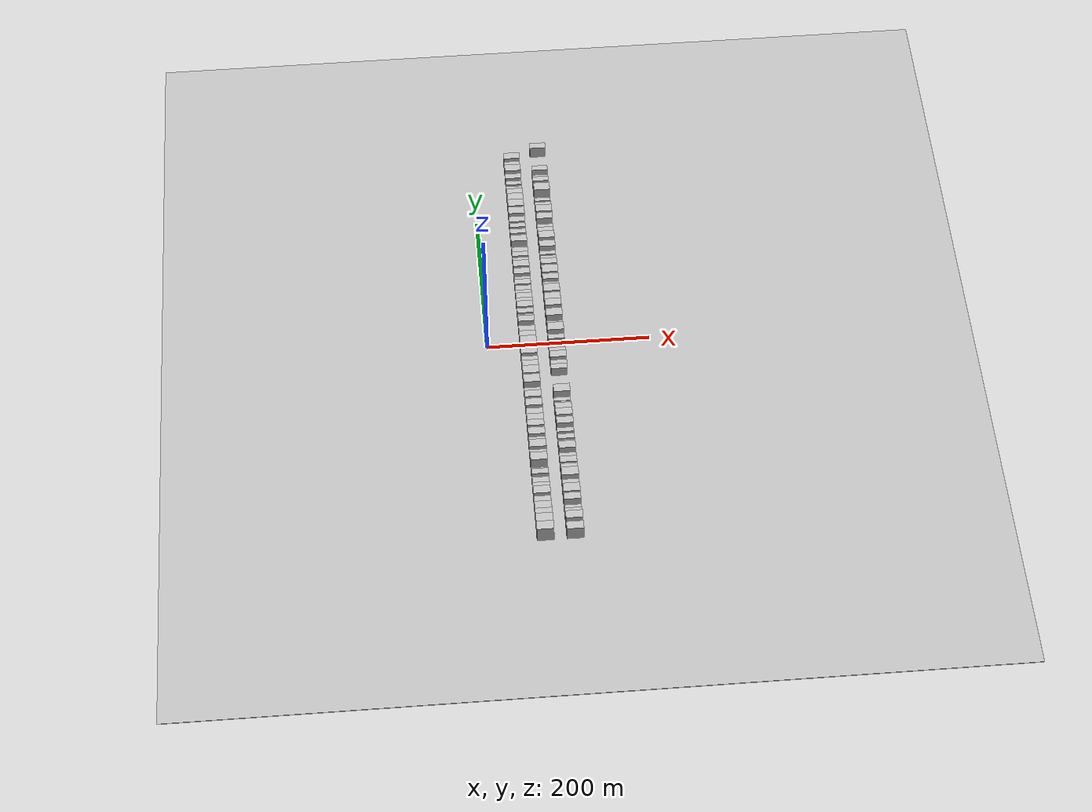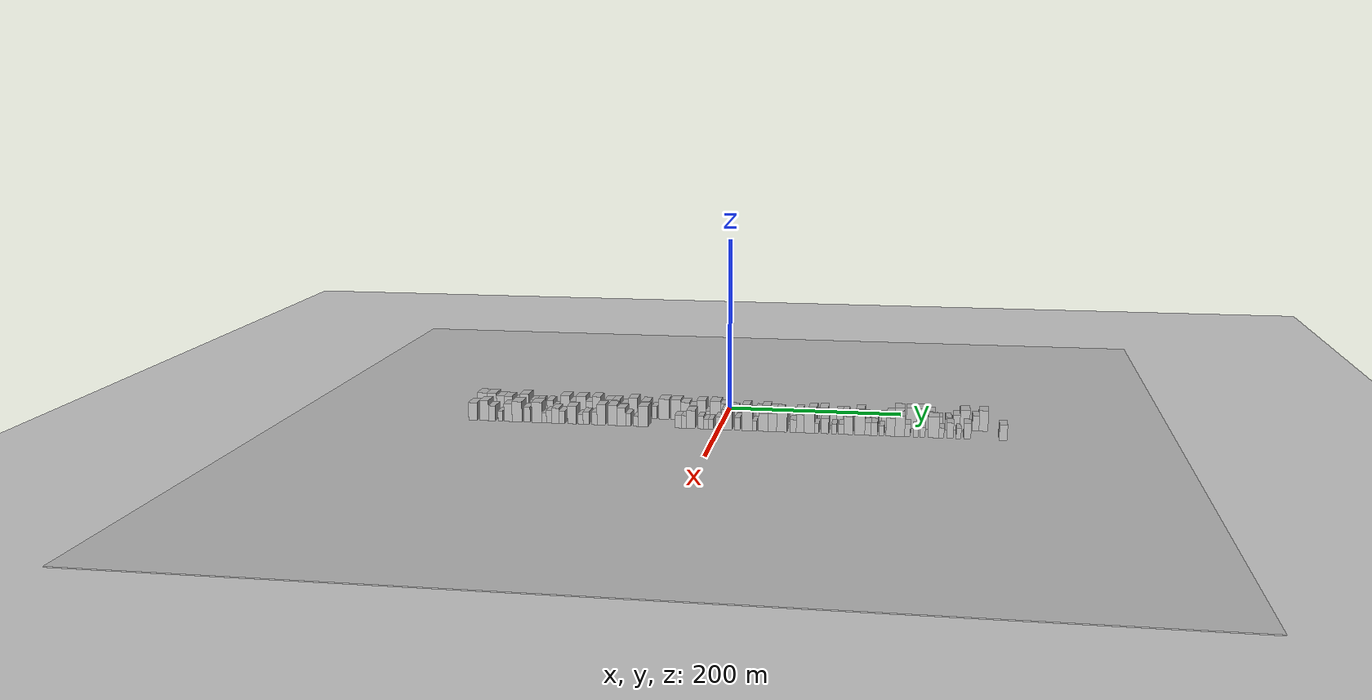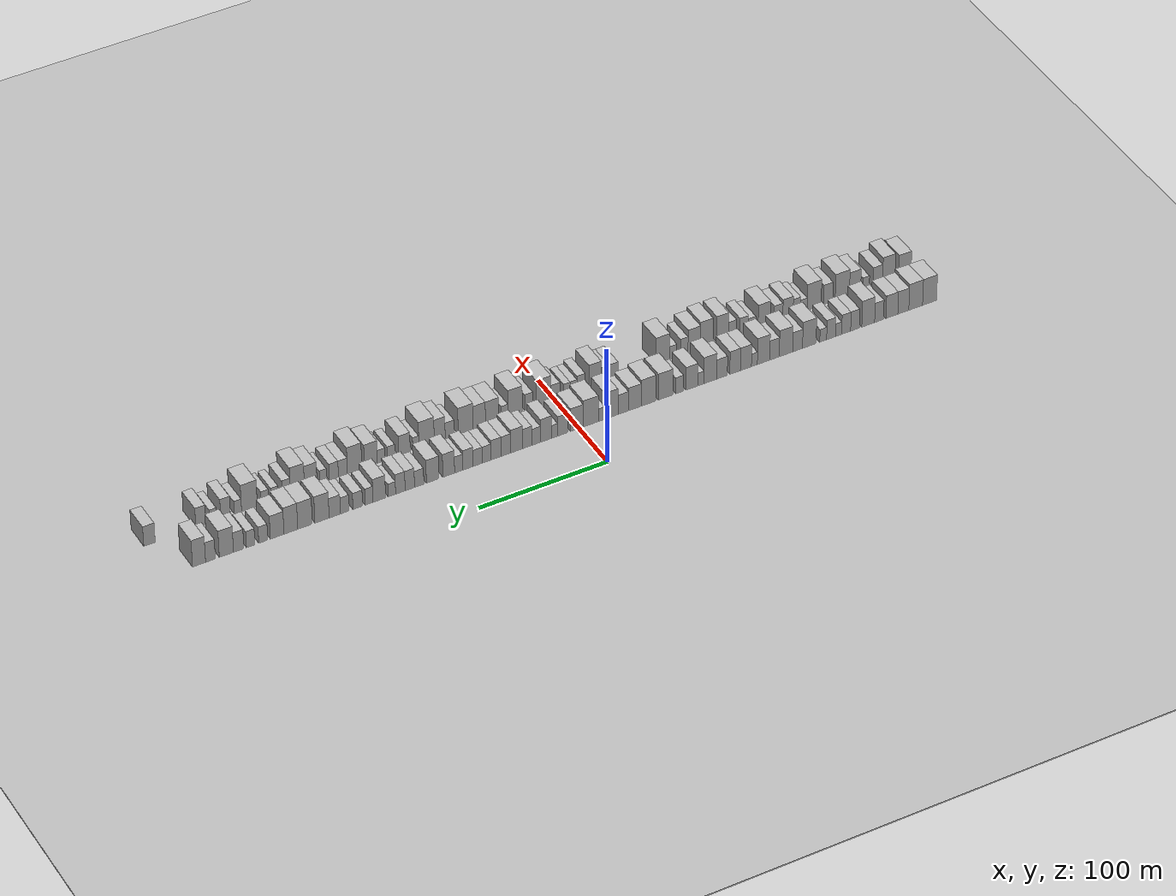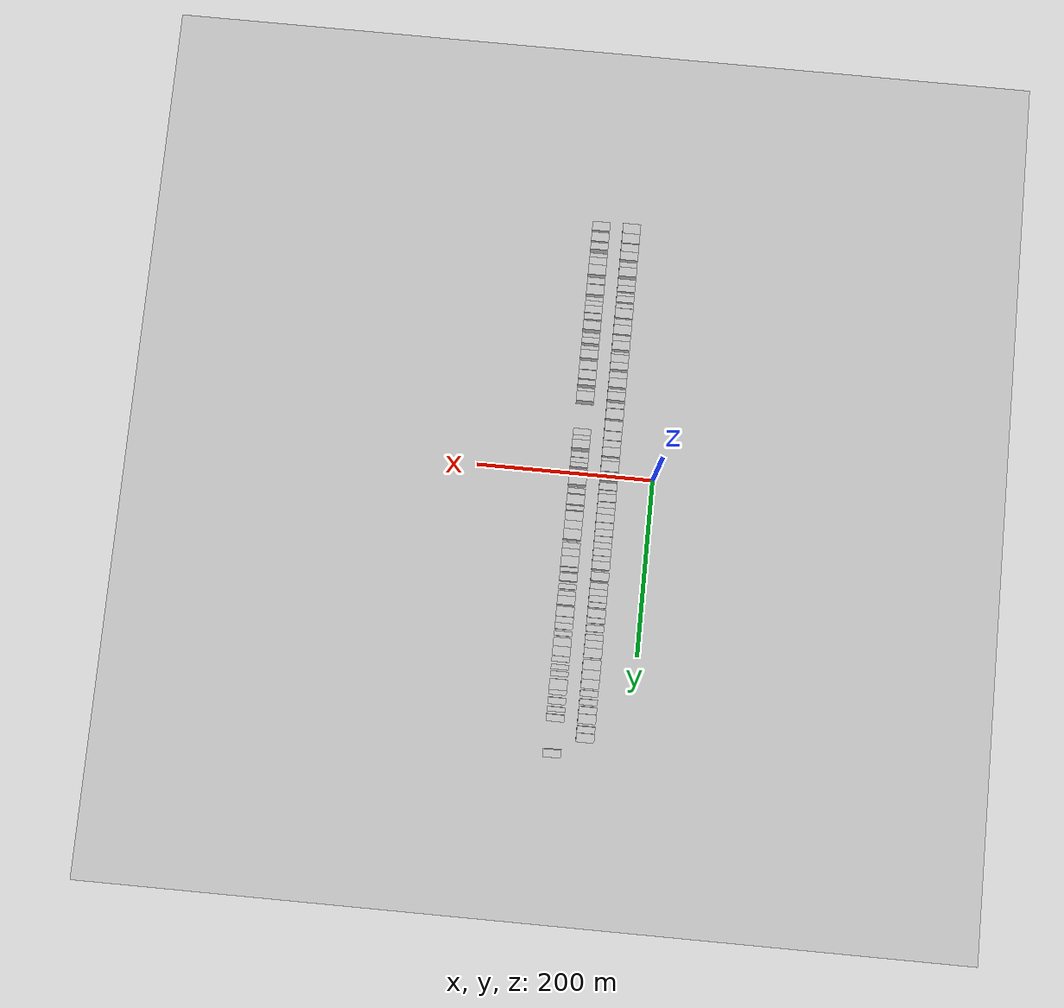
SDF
<?xml version="1.0" encoding="utf-8"?>

<sdf version="1.6">

   <world name="default">

      <gui fullscreen="0">

         <camera name="user_camera">

            <pose>-15 0 4.57585 0 0 0</pose>

            <view_controller>orbit</view_controller>

         </camera>

      </gui>

      <scene>

         <sky>

           <clouds>

             <speed>12</speed>

           </clouds>

         </sky>

         <ambient>0.4 0.4 0.4 1</ambient>

         <background>0.7 0.7 0.7 1</background>

         <shadows>1</shadows>

      </scene>

      <gravity>0 0 -9.8066</gravity>

      <magnetic_field>6e-06 2.3e-05 -4.2e-05</magnetic_field>

      <physics default="0" name="default_physics" type="ode">

         <ode>

            <solver>

               <type>quick</type>

               <iters>10</iters>

               <sor>1.0</sor>

               <use_dynamic_moi_rescaling>0</use_dynamic_moi_rescaling>

            </solver>

            <constraints>

               <cfm>0</cfm>

               <erp>0.2</erp>

               <contact_max_correcting_vel>100</contact_max_correcting_vel>

               <contact_surface_layer>0.001</contact_surface_layer>

            </constraints>

         </ode>

         <max_step_size>0.004</max_step_size>

         <real_time_factor>1</real_time_factor>

         <real_time_update_rate>250</real_time_update_rate>

      </physics>

      <light name="sun" type="directional">

         <cast_shadows>1</cast_shadows>

         <pose>0 0 10 0 0 0</pose>

         <diffuse>0.8 0.8 0.8 1</diffuse>

         <specular>0.2 0.2 0.2 1</specular>

         <attenuation>

            <range>1000</range>

            <constant>0.9</constant>

            <linear>0.01</linear>

            <quadratic>0.001</quadratic>

         </attenuation>

         <direction>-0.5 0.1 -0.9</direction>

      </light>

      <include>

         <name>ground_plane_1</name>

         <uri>model://HANNAS_ground_plane</uri>

         <pose>0 0 0  0 0 0</pose>

      </include>

      <include>

         <name>ground_plane_2</name>

         <uri>model://HANNAS_ground_plane</uri>

         <pose>100 0 0  0 0 0</pose>

      </include>

      <model name="building_1">

         <static>1</static>

         <pose frame="">50.0000 -284.1968 0 0.000000 0.000000 0.000000</pose>

         <link name="link">

            <pose frame="">0 0 12.00 0 0 0</pose>

            <collision name="collision">

               <geometry>

                  <box>

                     <size>20.0000 11.6064 24.0000</size>

                  </box>

               </geometry>

               <max_contacts>10</max_contacts>

               <surface>

                  <contact>

                     <ode/>

                  </contact>

                  <bounce/>

                  <friction>

                     <torsional>

                        <ode/>

                     </torsional>

                     <ode/>

                  </friction>

               </surface>

            </collision>

            <visual name="visual">

               <cast_shadows>0</cast_shadows>

               <geometry>

                  <box>

                     <size>20.0000 11.6064 24.0000</size>

                  </box>

               </geometry>

               <material>

                  <script>

                     <uri>model://HANNAS_wall/materials/scripts</uri>

                     <uri>model://HANNAS_wall/materials/textures</uri>

                     <name>vrc/HANNAS_wall</name>

                  </script>

               </material>

            </visual>

            <self_collide>0</self_collide>

            <enable_wind>0</enable_wind>

            <kinematic>0</kinematic>

         </link>

      </model>

      <model name="building_2">

         <static>1</static>

         <pose frame="">50.0000 -272.6836 0 0.000000 0.000000 0.000000</pose>

         <link name="link">

            <pose frame="">0 0 12.00 0 0 0</pose>

            <collision name="collision">

               <geometry>

                  <box>

                     <size>20.0000 11.4199 24.0000</size>

                  </box>

               </geometry>

               <max_contacts>10</max_contacts>

               <surface>

                  <contact>

                     <ode/>

                  </contact>

                  <bounce/>

                  <friction>

                     <torsional>

                        <ode/>

                     </torsional>

                     <ode/>

                  </friction>

               </surface>

            </collision>

            <visual name="visual">

               <cast_shadows>0</cast_shadows>

               <geometry>

                  <box>

                     <size>20.0000 11.4199 24.0000</size>

                  </box>

               </geometry>

               <material>

                  <script>

                     <uri>model://HANNAS_wall/materials/scripts</uri>

                     <uri>model://HANNAS_wall/materials/textures</uri>

                     <name>vrc/HANNAS_wall</name>

                  </script>

               </material>

            </visual>

            <self_collide>0</self_collide>

            <enable_wind>0</enable_wind>

            <kinematic>0</kinematic>

         </link>

      </model>

      <model name="building_3">

         <static>1</static>

         <pose frame="">50.0000 -262.4343 0 0.000000 0.000000 0.000000</pose>

         <link name="link">

            <pose frame="">0 0 10.50 0 0 0</pose>

            <collision name="collision">

               <geometry>

                  <box>

                     <size>20.0000 9.0788 21.0000</size>

                  </box>

               </geometry>

               <max_contacts>10</max_contacts>

               <surface>

                  <contact>

                     <ode/>

                  </contact>

                  <bounce/>

                  <friction>

                     <torsional>

                        <ode/>

                     </torsional>

                     <ode/>

                  </friction>

               </surface>

            </collision>

            <visual name="visual">

               <cast_shadows>0</cast_shadows>

               <geometry>

                  <box>

                     <size>20.0000 9.0788 21.0000</size>

                  </box>

               </geometry>

               <material>

                  <script>

                     <uri>model://HANNAS_wall/materials/scripts</uri>

                     <uri>model://HANNAS_wall/materials/textures</uri>

                     <name>vrc/HANNAS_wall</name>

                  </script>

               </material>

            </visual>

            <self_collide>0</self_collide>

            <enable_wind>0</enable_wind>

            <kinematic>0</kinematic>

         </link>

      </model>

      <model name="building_4">

         <static>1</static>

         <pose frame="">50.0000 -252.9656 0 0.000000 0.000000 0.000000</pose>

         <link name="link">

            <pose frame="">0 0 10.50 0 0 0</pose>

            <collision name="collision">

               <geometry>

                  <box>

                     <size>20.0000 9.8587 21.0000</size>

                  </box>

               </geometry>

               <max_contacts>10</max_contacts>

               <surface>

                  <contact>

                     <ode/>

                  </contact>

                  <bounce/>

                  <friction>

                     <torsional>

                        <ode/>

                     </torsional>

                     <ode/>

                  </friction>

               </surface>

            </collision>

            <visual name="visual">

               <cast_shadows>0</cast_shadows>

               <geometry>

                  <box>

                     <size>20.0000 9.8587 21.0000</size>

                  </box>

               </geometry>

               <material>

                  <script>

                     <uri>model://HANNAS_wall/materials/scripts</uri>

                     <uri>model://HANNAS_wall/materials/textures</uri>

                     <name>vrc/HANNAS_wall</name>

                  </script>

               </material>

            </visual>

            <self_collide>0</self_collide>

            <enable_wind>0</enable_wind>

            <kinematic>0</kinematic>

         </link>

      </model>

      <model name="building_5">

         <static>1</static>

         <pose frame="">50.0000 -242.3682 0 0.000000 0.000000 0.000000</pose>

         <link name="link">

            <pose frame="">0 0 9.00 0 0 0</pose>

            <collision name="collision">

               <geometry>

                  <box>

                     <size>20.0000 7.3362 18.0000</size>

                  </box>

               </geometry>

               <max_contacts>10</max_contacts>

               <surface>

                  <contact>

                     <ode/>

                  </contact>

                  <bounce/>

                  <friction>

                     <torsional>

                        <ode/>

                     </torsional>

                     <ode/>

                  </friction>

               </surface>

            </collision>

            <visual name="visual">

               <cast_shadows>0</cast_shadows>

               <geometry>

                  <box>

                     <size>20.0000 7.3362 18.0000</size>

                  </box>

               </geometry>

               <material>

                  <script>

                     <uri>model://HANNAS_wall/materials/scripts</uri>

                     <uri>model://HANNAS_wall/materials/textures</uri>

                     <name>vrc/HANNAS_wall</name>

                  </script>

               </material>

            </visual>

            <self_collide>0</self_collide>

            <enable_wind>0</enable_wind>

            <kinematic>0</kinematic>

         </link>

      </model>

      <model name="building_6">

         <static>1</static>

         <pose frame="">50.0000 -233.4100 0 0.000000 0.000000 0.000000</pose>

         <link name="link">

            <pose frame="">0 0 12.00 0 0 0</pose>

            <collision name="collision">

               <geometry>

                  <box>

                     <size>20.0000 10.5801 24.0000</size>

                  </box>

               </geometry>

               <max_contacts>10</max_contacts>

               <surface>

                  <contact>

                     <ode/>

                  </contact>

                  <bounce/>

                  <friction>

                     <torsional>

                        <ode/>

                     </torsional>

                     <ode/>

                  </friction>

               </surface>

            </collision>

            <visual name="visual">

               <cast_shadows>0</cast_shadows>

               <geometry>

                  <box>

                     <size>20.0000 10.5801 24.0000</size>

                  </box>

               </geometry>

               <material>

                  <script>

                     <uri>model://HANNAS_wall/materials/scripts</uri>

                     <uri>model://HANNAS_wall/materials/textures</uri>

                     <name>vrc/HANNAS_wall</name>

                  </script>

               </material>

            </visual>

            <self_collide>0</self_collide>

            <enable_wind>0</enable_wind>

            <kinematic>0</kinematic>

         </link>

      </model>

      <model name="building_7">

         <static>1</static>

         <pose frame="">50.0000 -222.5193 0 0.000000 0.000000 0.000000</pose>

         <link name="link">

            <pose frame="">0 0 9.00 0 0 0</pose>

            <collision name="collision">

               <geometry>

                  <box>

                     <size>20.0000 7.2013 18.0000</size>

                  </box>

               </geometry>

               <max_contacts>10</max_contacts>

               <surface>

                  <contact>

                     <ode/>

                  </contact>

                  <bounce/>

                  <friction>

                     <torsional>

                        <ode/>

                     </torsional>

                     <ode/>

                  </friction>

               </surface>

            </collision>

            <visual name="visual">

               <cast_shadows>0</cast_shadows>

               <geometry>

                  <box>

                     <size>20.0000 7.2013 18.0000</size>

                  </box>

               </geometry>

               <material>

                  <script>

                     <uri>model://HANNAS_wall/materials/scripts</uri>

                     <uri>model://HANNAS_wall/materials/textures</uri>

                     <name>vrc/HANNAS_wall</name>

                  </script>

               </material>

            </visual>

            <self_collide>0</self_collide>

            <enable_wind>0</enable_wind>

            <kinematic>0</kinematic>

         </link>

      </model>

      <model name="building_8">

         <static>1</static>

         <pose frame="">50.0000 -215.2438 0 0.000000 0.000000 0.000000</pose>

         <link name="link">

            <pose frame="">0 0 9.00 0 0 0</pose>

            <collision name="collision">

               <geometry>

                  <box>

                     <size>20.0000 7.3496 18.0000</size>

                  </box>

               </geometry>

               <max_contacts>10</max_contacts>

               <surface>

                  <contact>

                     <ode/>

                  </contact>

                  <bounce/>

                  <friction>

                     <torsional>

                        <ode/>

                     </torsional>

                     <ode/>

                  </friction>

               </surface>

            </collision>

            <visual name="visual">

               <cast_shadows>0</cast_shadows>

               <geometry>

                  <box>

                     <size>20.0000 7.3496 18.0000</size>

                  </box>

               </geometry>

               <material>

                  <script>

                     <uri>model://HANNAS_wall/materials/scripts</uri>

                     <uri>model://HANNAS_wall/materials/textures</uri>

                     <name>vrc/HANNAS_wall</name>

                  </script>

               </material>

            </visual>

            <self_collide>0</self_collide>

            <enable_wind>0</enable_wind>

            <kinematic>0</kinematic>

         </link>

      </model>

      <model name="building_9">

         <static>1</static>

         <pose frame="">50.0000 -209.0613 0 0.000000 0.000000 0.000000</pose>

         <link name="link">

            <pose frame="">0 0 6.00 0 0 0</pose>

            <collision name="collision">

               <geometry>

                  <box>

                     <size>20.0000 5.0154 12.0000</size>

                  </box>

               </geometry>

               <max_contacts>10</max_contacts>

               <surface>

                  <contact>

                     <ode/>

                  </contact>

                  <bounce/>

                  <friction>

                     <torsional>

                        <ode/>

                     </torsional>

                     <ode/>

                  </friction>

               </surface>

            </collision>

            <visual name="visual">

               <cast_shadows>0</cast_shadows>

               <geometry>

                  <box>

                     <size>20.0000 5.0154 12.0000</size>

                  </box>

               </geometry>

               <material>

                  <script>

                     <uri>model://HANNAS_wall/materials/scripts</uri>

                     <uri>model://HANNAS_wall/materials/textures</uri>

                     <name>vrc/HANNAS_wall</name>

                  </script>

               </material>

            </visual>

            <self_collide>0</self_collide>

            <enable_wind>0</enable_wind>

            <kinematic>0</kinematic>

         </link>

      </model>

      <model name="building_10">

         <static>1</static>

         <pose frame="">50.0000 -202.8698 0 0.000000 0.000000 0.000000</pose>

         <link name="link">

            <pose frame="">0 0 9.00 0 0 0</pose>

            <collision name="collision">

               <geometry>

                  <box>

                     <size>20.0000 7.3677 18.0000</size>

                  </box>

               </geometry>

               <max_contacts>10</max_contacts>

               <surface>

                  <contact>

                     <ode/>

                  </contact>

                  <bounce/>

                  <friction>

                     <torsional>

                        <ode/>

                     </torsional>

                     <ode/>

                  </friction>

               </surface>

            </collision>

            <visual name="visual">

               <cast_shadows>0</cast_shadows>

               <geometry>

                  <box>

                     <size>20.0000 7.3677 18.0000</size>

                  </box>

               </geometry>

               <material>

                  <script>

                     <uri>model://HANNAS_wall/materials/scripts</uri>

                     <uri>model://HANNAS_wall/materials/textures</uri>

                     <name>vrc/HANNAS_wall</name>

                  </script>

               </material>

            </visual>

            <self_collide>0</self_collide>

            <enable_wind>0</enable_wind>

            <kinematic>0</kinematic>

         </link>

      </model>

      <model name="building_11">

         <static>1</static>

         <pose frame="">50.0000 -196.3837 0 0.000000 0.000000 0.000000</pose>

         <link name="link">

            <pose frame="">0 0 6.00 0 0 0</pose>

            <collision name="collision">

               <geometry>

                  <box>

                     <size>20.0000 5.6044 12.0000</size>

                  </box>

               </geometry>

               <max_contacts>10</max_contacts>

               <surface>

                  <contact>

                     <ode/>

                  </contact>

                  <bounce/>

                  <friction>

                     <torsional>

                        <ode/>

                     </torsional>

                     <ode/>

                  </friction>

               </surface>

            </collision>

            <visual name="visual">

               <cast_shadows>0</cast_shadows>

               <geometry>

                  <box>

                     <size>20.0000 5.6044 12.0000</size>

                  </box>

               </geometry>

               <material>

                  <script>

                     <uri>model://HANNAS_wall/materials/scripts</uri>

                     <uri>model://HANNAS_wall/materials/textures</uri>

                     <name>vrc/HANNAS_wall</name>

                  </script>

               </material>

            </visual>

            <self_collide>0</self_collide>

            <enable_wind>0</enable_wind>

            <kinematic>0</kinematic>

         </link>

      </model>

      <model name="building_12">

         <static>1</static>

         <pose frame="">50.0000 -185.0307 0 0.000000 0.000000 0.000000</pose>

         <link name="link">

            <pose frame="">0 0 12.00 0 0 0</pose>

            <collision name="collision">

               <geometry>

                  <box>

                     <size>20.0000 11.1017 24.0000</size>

                  </box>

               </geometry>

               <max_contacts>10</max_contacts>

               <surface>

                  <contact>

                     <ode/>

                  </contact>

                  <bounce/>

                  <friction>

                     <torsional>

                        <ode/>

                     </torsional>

                     <ode/>

                  </friction>

               </surface>

            </collision>

            <visual name="visual">

               <cast_shadows>0</cast_shadows>

               <geometry>

                  <box>

                     <size>20.0000 11.1017 24.0000</size>

                  </box>

               </geometry>

               <material>

                  <script>

                     <uri>model://HANNAS_wall/materials/scripts</uri>

                     <uri>model://HANNAS_wall/materials/textures</uri>

                     <name>vrc/HANNAS_wall</name>

                  </script>

               </material>

            </visual>

            <self_collide>0</self_collide>

            <enable_wind>0</enable_wind>

            <kinematic>0</kinematic>

         </link>

      </model>

      <model name="building_13">

         <static>1</static>

         <pose frame="">50.0000 -175.4873 0 0.000000 0.000000 0.000000</pose>

         <link name="link">

            <pose frame="">0 0 9.00 0 0 0</pose>

            <collision name="collision">

               <geometry>

                  <box>

                     <size>20.0000 7.9851 18.0000</size>

                  </box>

               </geometry>

               <max_contacts>10</max_contacts>

               <surface>

                  <contact>

                     <ode/>

                  </contact>

                  <bounce/>

                  <friction>

                     <torsional>

                        <ode/>

                     </torsional>

                     <ode/>

                  </friction>

               </surface>

            </collision>

            <visual name="visual">

               <cast_shadows>0</cast_shadows>

               <geometry>

                  <box>

                     <size>20.0000 7.9851 18.0000</size>

                  </box>

               </geometry>

               <material>

                  <script>

                     <uri>model://HANNAS_wall/materials/scripts</uri>

                     <uri>model://HANNAS_wall/materials/textures</uri>

                     <name>vrc/HANNAS_wall</name>

                  </script>

               </material>

            </visual>

            <self_collide>0</self_collide>

            <enable_wind>0</enable_wind>

            <kinematic>0</kinematic>

         </link>

      </model>

      <model name="building_14">

         <static>1</static>

         <pose frame="">50.0000 -166.0058 0 0.000000 0.000000 0.000000</pose>

         <link name="link">

            <pose frame="">0 0 12.00 0 0 0</pose>

            <collision name="collision">

               <geometry>

                  <box>

                     <size>20.0000 10.9779 24.0000</size>

                  </box>

               </geometry>

               <max_contacts>10</max_contacts>

               <surface>

                  <contact>

                     <ode/>

                  </contact>

                  <bounce/>

                  <friction>

                     <torsional>

                        <ode/>

                     </torsional>

                     <ode/>

                  </friction>

               </surface>

            </collision>

            <visual name="visual">

               <cast_shadows>0</cast_shadows>

               <geometry>

                  <box>

                     <size>20.0000 10.9779 24.0000</size>

                  </box>

               </geometry>

               <material>

                  <script>

                     <uri>model://HANNAS_wall/materials/scripts</uri>

                     <uri>model://HANNAS_wall/materials/textures</uri>

                     <name>vrc/HANNAS_wall</name>

                  </script>

               </material>

            </visual>

            <self_collide>0</self_collide>

            <enable_wind>0</enable_wind>

            <kinematic>0</kinematic>

         </link>

      </model>

      <model name="building_15">

         <static>1</static>

         <pose frame="">50.0000 -156.6610 0 0.000000 0.000000 0.000000</pose>

         <link name="link">

            <pose frame="">0 0 9.00 0 0 0</pose>

            <collision name="collision">

               <geometry>

                  <box>

                     <size>20.0000 7.7117 18.0000</size>

                  </box>

               </geometry>

               <max_contacts>10</max_contacts>

               <surface>

                  <contact>

                     <ode/>

                  </contact>

                  <bounce/>

                  <friction>

                     <torsional>

                        <ode/>

                     </torsional>

                     <ode/>

                  </friction>

               </surface>

            </collision>

            <visual name="visual">

               <cast_shadows>0</cast_shadows>

               <geometry>

                  <box>

                     <size>20.0000 7.7117 18.0000</size>

                  </box>

               </geometry>

               <material>

                  <script>

                     <uri>model://HANNAS_wall/materials/scripts</uri>

                     <uri>model://HANNAS_wall/materials/textures</uri>

                     <name>vrc/HANNAS_wall</name>

                  </script>

               </material>

            </visual>

            <self_collide>0</self_collide>

            <enable_wind>0</enable_wind>

            <kinematic>0</kinematic>

         </link>

      </model>

      <model name="building_16">

         <static>1</static>

         <pose frame="">50.0000 -147.7419 0 0.000000 0.000000 0.000000</pose>

         <link name="link">

            <pose frame="">0 0 12.00 0 0 0</pose>

            <collision name="collision">

               <geometry>

                  <box>

                     <size>20.0000 10.1264 24.0000</size>

                  </box>

               </geometry>

               <max_contacts>10</max_contacts>

               <surface>

                  <contact>

                     <ode/>

                  </contact>

                  <bounce/>

                  <friction>

                     <torsional>

                        <ode/>

                     </torsional>

                     <ode/>

                  </friction>

               </surface>

            </collision>

            <visual name="visual">

               <cast_shadows>0</cast_shadows>

               <geometry>

                  <box>

                     <size>20.0000 10.1264 24.0000</size>

                  </box>

               </geometry>

               <material>

                  <script>

                     <uri>model://HANNAS_wall/materials/scripts</uri>

                     <uri>model://HANNAS_wall/materials/textures</uri>

                     <name>vrc/HANNAS_wall</name>

                  </script>

               </material>

            </visual>

            <self_collide>0</self_collide>

            <enable_wind>0</enable_wind>

            <kinematic>0</kinematic>

         </link>

      </model>

      <model name="building_17">

         <static>1</static>

         <pose frame="">50.0000 -140.2602 0 0.000000 0.000000 0.000000</pose>

         <link name="link">

            <pose frame="">0 0 6.00 0 0 0</pose>

            <collision name="collision">

               <geometry>

                  <box>

                     <size>20.0000 4.8370 12.0000</size>

                  </box>

               </geometry>

               <max_contacts>10</max_contacts>

               <surface>

                  <contact>

                     <ode/>

                  </contact>

                  <bounce/>

                  <friction>

                     <torsional>

                        <ode/>

                     </torsional>

                     <ode/>

                  </friction>

               </surface>

            </collision>

            <visual name="visual">

               <cast_shadows>0</cast_shadows>

               <geometry>

                  <box>

                     <size>20.0000 4.8370 12.0000</size>

                  </box>

               </geometry>

               <material>

                  <script>

                     <uri>model://HANNAS_wall/materials/scripts</uri>

                     <uri>model://HANNAS_wall/materials/textures</uri>

                     <name>vrc/HANNAS_wall</name>

                  </script>

               </material>

            </visual>

            <self_collide>0</self_collide>

            <enable_wind>0</enable_wind>

            <kinematic>0</kinematic>

         </link>

      </model>

      <model name="building_18">

         <static>1</static>

         <pose frame="">50.0000 -133.3484 0 0.000000 0.000000 0.000000</pose>

         <link name="link">

            <pose frame="">0 0 10.50 0 0 0</pose>

            <collision name="collision">

               <geometry>

                  <box>

                     <size>20.0000 8.9866 21.0000</size>

                  </box>

               </geometry>

               <max_contacts>10</max_contacts>

               <surface>

                  <contact>

                     <ode/>

                  </contact>

                  <bounce/>

                  <friction>

                     <torsional>

                        <ode/>

                     </torsional>

                     <ode/>

                  </friction>

               </surface>

            </collision>

            <visual name="visual">

               <cast_shadows>0</cast_shadows>

               <geometry>

                  <box>

                     <size>20.0000 8.9866 21.0000</size>

                  </box>

               </geometry>

               <material>

                  <script>

                     <uri>model://HANNAS_wall/materials/scripts</uri>

                     <uri>model://HANNAS_wall/materials/textures</uri>

                     <name>vrc/HANNAS_wall</name>

                  </script>

               </material>

            </visual>

            <self_collide>0</self_collide>

            <enable_wind>0</enable_wind>

            <kinematic>0</kinematic>

         </link>

      </model>

      <model name="building_19">

         <static>1</static>

         <pose frame="">50.0000 -124.6117 0 0.000000 0.000000 0.000000</pose>

         <link name="link">

            <pose frame="">0 0 10.50 0 0 0</pose>

            <collision name="collision">

               <geometry>

                  <box>

                     <size>20.0000 8.4868 21.0000</size>

                  </box>

               </geometry>

               <max_contacts>10</max_contacts>

               <surface>

                  <contact>

                     <ode/>

                  </contact>

                  <bounce/>

                  <friction>

                     <torsional>

                        <ode/>

                     </torsional>

                     <ode/>

                  </friction>

               </surface>

            </collision>

            <visual name="visual">

               <cast_shadows>0</cast_shadows>

               <geometry>

                  <box>

                     <size>20.0000 8.4868 21.0000</size>

                  </box>

               </geometry>

               <material>

                  <script>

                     <uri>model://HANNAS_wall/materials/scripts</uri>

                     <uri>model://HANNAS_wall/materials/textures</uri>

                     <name>vrc/HANNAS_wall</name>

                  </script>

               </material>

            </visual>

            <self_collide>0</self_collide>

            <enable_wind>0</enable_wind>

            <kinematic>0</kinematic>

         </link>

      </model>

      <model name="building_20">

         <static>1</static>

         <pose frame="">50.0000 -114.1326 0 0.000000 0.000000 0.000000</pose>

         <link name="link">

            <pose frame="">0 0 9.00 0 0 0</pose>

            <collision name="collision">

               <geometry>

                  <box>

                     <size>20.0000 8.4714 18.0000</size>

                  </box>

               </geometry>

               <max_contacts>10</max_contacts>

               <surface>

                  <contact>

                     <ode/>

                  </contact>

                  <bounce/>

                  <friction>

                     <torsional>

                        <ode/>

                     </torsional>

                     <ode/>

                  </friction>

               </surface>

            </collision>

            <visual name="visual">

               <cast_shadows>0</cast_shadows>

               <geometry>

                  <box>

                     <size>20.0000 8.4714 18.0000</size>

                  </box>

               </geometry>

               <material>

                  <script>

                     <uri>model://HANNAS_wall/materials/scripts</uri>

                     <uri>model://HANNAS_wall/materials/textures</uri>

                     <name>vrc/HANNAS_wall</name>

                  </script>

               </material>

            </visual>

            <self_collide>0</self_collide>

            <enable_wind>0</enable_wind>

            <kinematic>0</kinematic>

         </link>

      </model>

      <model name="building_21">

         <static>1</static>

         <pose frame="">50.0000 -104.7004 0 0.000000 0.000000 0.000000</pose>

         <link name="link">

            <pose frame="">0 0 12.00 0 0 0</pose>

            <collision name="collision">

               <geometry>

                  <box>

                     <size>20.0000 10.3930 24.0000</size>

                  </box>

               </geometry>

               <max_contacts>10</max_contacts>

               <surface>

                  <contact>

                     <ode/>

                  </contact>

                  <bounce/>

                  <friction>

                     <torsional>

                        <ode/>

                     </torsional>

                     <ode/>

                  </friction>

               </surface>

            </collision>

            <visual name="visual">

               <cast_shadows>0</cast_shadows>

               <geometry>

                  <box>

                     <size>20.0000 10.3930 24.0000</size>

                  </box>

               </geometry>

               <material>

                  <script>

                     <uri>model://HANNAS_wall/materials/scripts</uri>

                     <uri>model://HANNAS_wall/materials/textures</uri>

                     <name>vrc/HANNAS_wall</name>

                  </script>

               </material>

            </visual>

            <self_collide>0</self_collide>

            <enable_wind>0</enable_wind>

            <kinematic>0</kinematic>

         </link>

      </model>

      <model name="building_22">

         <static>1</static>

         <pose frame="">50.0000 -97.0555 0 0.000000 0.000000 0.000000</pose>

         <link name="link">

            <pose frame="">0 0 6.00 0 0 0</pose>

            <collision name="collision">

               <geometry>

                  <box>

                     <size>20.0000 4.8968 12.0000</size>

                  </box>

               </geometry>

               <max_contacts>10</max_contacts>

               <surface>

                  <contact>

                     <ode/>

                  </contact>

                  <bounce/>

                  <friction>

                     <torsional>

                        <ode/>

                     </torsional>

                     <ode/>

                  </friction>

               </surface>

            </collision>

            <visual name="visual">

               <cast_shadows>0</cast_shadows>

               <geometry>

                  <box>

                     <size>20.0000 4.8968 12.0000</size>

                  </box>

               </geometry>

               <material>

                  <script>

                     <uri>model://HANNAS_wall/materials/scripts</uri>

                     <uri>model://HANNAS_wall/materials/textures</uri>

                     <name>vrc/HANNAS_wall</name>

                  </script>

               </material>

            </visual>

            <self_collide>0</self_collide>

            <enable_wind>0</enable_wind>

            <kinematic>0</kinematic>

         </link>

      </model>

      <model name="building_23">

         <static>1</static>

         <pose frame="">50.0000 -89.8188 0 0.000000 0.000000 0.000000</pose>

         <link name="link">

            <pose frame="">0 0 10.50 0 0 0</pose>

            <collision name="collision">

               <geometry>

                  <box>

                     <size>20.0000 9.5765 21.0000</size>

                  </box>

               </geometry>

               <max_contacts>10</max_contacts>

               <surface>

                  <contact>

                     <ode/>

                  </contact>

                  <bounce/>

                  <friction>

                     <torsional>

                        <ode/>

                     </torsional>

                     <ode/>

                  </friction>

               </surface>

            </collision>

            <visual name="visual">

               <cast_shadows>0</cast_shadows>

               <geometry>

                  <box>

                     <size>20.0000 9.5765 21.0000</size>

                  </box>

               </geometry>

               <material>

                  <script>

                     <uri>model://HANNAS_wall/materials/scripts</uri>

                     <uri>model://HANNAS_wall/materials/textures</uri>

                     <name>vrc/HANNAS_wall</name>

                  </script>

               </material>

            </visual>

            <self_collide>0</self_collide>

            <enable_wind>0</enable_wind>

            <kinematic>0</kinematic>

         </link>

      </model>

      <model name="building_24">

         <static>1</static>

         <pose frame="">50.0000 -79.8754 0 0.000000 0.000000 0.000000</pose>

         <link name="link">

            <pose frame="">0 0 7.50 0 0 0</pose>

            <collision name="collision">

               <geometry>

                  <box>

                     <size>20.0000 6.3102 15.0000</size>

                  </box>

               </geometry>

               <max_contacts>10</max_contacts>

               <surface>

                  <contact>

                     <ode/>

                  </contact>

                  <bounce/>

                  <friction>

                     <torsional>

                        <ode/>

                     </torsional>

                     <ode/>

                  </friction>

               </surface>

            </collision>

            <visual name="visual">

               <cast_shadows>0</cast_shadows>

               <geometry>

                  <box>

                     <size>20.0000 6.3102 15.0000</size>

                  </box>

               </geometry>

               <material>

                  <script>

                     <uri>model://HANNAS_wall/materials/scripts</uri>

                     <uri>model://HANNAS_wall/materials/textures</uri>

                     <name>vrc/HANNAS_wall</name>

                  </script>

               </material>

            </visual>

            <self_collide>0</self_collide>

            <enable_wind>0</enable_wind>

            <kinematic>0</kinematic>

         </link>

      </model>

      <model name="building_25">

         <static>1</static>

         <pose frame="">50.0000 -68.7800 0 0.000000 0.000000 0.000000</pose>

         <link name="link">

            <pose frame="">0 0 12.00 0 0 0</pose>

            <collision name="collision">

               <geometry>

                  <box>

                     <size>20.0000 11.8807 24.0000</size>

                  </box>

               </geometry>

               <max_contacts>10</max_contacts>

               <surface>

                  <contact>

                     <ode/>

                  </contact>

                  <bounce/>

                  <friction>

                     <torsional>

                        <ode/>

                     </torsional>

                     <ode/>

                  </friction>

               </surface>

            </collision>

            <visual name="visual">

               <cast_shadows>0</cast_shadows>

               <geometry>

                  <box>

                     <size>20.0000 11.8807 24.0000</size>

                  </box>

               </geometry>

               <material>

                  <script>

                     <uri>model://HANNAS_wall/materials/scripts</uri>

                     <uri>model://HANNAS_wall/materials/textures</uri>

                     <name>vrc/HANNAS_wall</name>

                  </script>

               </material>

            </visual>

            <self_collide>0</self_collide>

            <enable_wind>0</enable_wind>

            <kinematic>0</kinematic>

         </link>

      </model>

      <model name="building_26">

         <static>1</static>

         <pose frame="">50.0000 -55.0351 0 0.000000 0.000000 0.000000</pose>

         <link name="link">

            <pose frame="">0 0 12.00 0 0 0</pose>

            <collision name="collision">

               <geometry>

                  <box>

                     <size>20.0000 11.6092 24.0000</size>

                  </box>

               </geometry>

               <max_contacts>10</max_contacts>

               <surface>

                  <contact>

                     <ode/>

                  </contact>

                  <bounce/>

                  <friction>

                     <torsional>

                        <ode/>

                     </torsional>

                     <ode/>

                  </friction>

               </surface>

            </collision>

            <visual name="visual">

               <cast_shadows>0</cast_shadows>

               <geometry>

                  <box>

                     <size>20.0000 11.6092 24.0000</size>

                  </box>

               </geometry>

               <material>

                  <script>

                     <uri>model://HANNAS_wall/materials/scripts</uri>

                     <uri>model://HANNAS_wall/materials/textures</uri>

                     <name>vrc/HANNAS_wall</name>

                  </script>

               </material>

            </visual>

            <self_collide>0</self_collide>

            <enable_wind>0</enable_wind>

            <kinematic>0</kinematic>

         </link>

      </model>

      <model name="building_27">

         <static>1</static>

         <pose frame="">50.0000 -44.1194 0 0.000000 0.000000 0.000000</pose>

         <link name="link">

            <pose frame="">0 0 10.50 0 0 0</pose>

            <collision name="collision">

               <geometry>

                  <box>

                     <size>20.0000 10.2222 21.0000</size>

                  </box>

               </geometry>

               <max_contacts>10</max_contacts>

               <surface>

                  <contact>

                     <ode/>

                  </contact>

                  <bounce/>

                  <friction>

                     <torsional>

                        <ode/>

                     </torsional>

                     <ode/>

                  </friction>

               </surface>

            </collision>

            <visual name="visual">

               <cast_shadows>0</cast_shadows>

               <geometry>

                  <box>

                     <size>20.0000 10.2222 21.0000</size>

                  </box>

               </geometry>

               <material>

                  <script>

                     <uri>model://HANNAS_wall/materials/scripts</uri>

                     <uri>model://HANNAS_wall/materials/textures</uri>

                     <name>vrc/HANNAS_wall</name>

                  </script>

               </material>

            </visual>

            <self_collide>0</self_collide>

            <enable_wind>0</enable_wind>

            <kinematic>0</kinematic>

         </link>

      </model>

      <model name="building_28">

         <static>1</static>

         <pose frame="">50.0000 -34.8238 0 0.000000 0.000000 0.000000</pose>

         <link name="link">

            <pose frame="">0 0 9.00 0 0 0</pose>

            <collision name="collision">

               <geometry>

                  <box>

                     <size>20.0000 8.3691 18.0000</size>

                  </box>

               </geometry>

               <max_contacts>10</max_contacts>

               <surface>

                  <contact>

                     <ode/>

                  </contact>

                  <bounce/>

                  <friction>

                     <torsional>

                        <ode/>

                     </torsional>

                     <ode/>

                  </friction>

               </surface>

            </collision>

            <visual name="visual">

               <cast_shadows>0</cast_shadows>

               <geometry>

                  <box>

                     <size>20.0000 8.3691 18.0000</size>

                  </box>

               </geometry>

               <material>

                  <script>

                     <uri>model://HANNAS_wall/materials/scripts</uri>

                     <uri>model://HANNAS_wall/materials/textures</uri>

                     <name>vrc/HANNAS_wall</name>

                  </script>

               </material>

            </visual>

            <self_collide>0</self_collide>

            <enable_wind>0</enable_wind>

            <kinematic>0</kinematic>

         </link>

      </model>

      <model name="building_29">

         <static>1</static>

         <pose frame="">50.0000 -25.4632 0 0.000000 0.000000 0.000000</pose>

         <link name="link">

            <pose frame="">0 0 12.00 0 0 0</pose>

            <collision name="collision">

               <geometry>

                  <box>

                     <size>20.0000 10.3520 24.0000</size>

                  </box>

               </geometry>

               <max_contacts>10</max_contacts>

               <surface>

                  <contact>

                     <ode/>

                  </contact>

                  <bounce/>

                  <friction>

                     <torsional>

                        <ode/>

                     </torsional>

                     <ode/>

                  </friction>

               </surface>

            </collision>

            <visual name="visual">

               <cast_shadows>0</cast_shadows>

               <geometry>

                  <box>

                     <size>20.0000 10.3520 24.0000</size>

                  </box>

               </geometry>

               <material>

                  <script>

                     <uri>model://HANNAS_wall/materials/scripts</uri>

                     <uri>model://HANNAS_wall/materials/textures</uri>

                     <name>vrc/HANNAS_wall</name>

                  </script>

               </material>

            </visual>

            <self_collide>0</self_collide>

            <enable_wind>0</enable_wind>

            <kinematic>0</kinematic>

         </link>

      </model>

      <model name="building_30">

         <static>1</static>

         <pose frame="">50.0000 -17.6929 0 0.000000 0.000000 0.000000</pose>

         <link name="link">

            <pose frame="">0 0 6.00 0 0 0</pose>

            <collision name="collision">

               <geometry>

                  <box>

                     <size>20.0000 5.1887 12.0000</size>

                  </box>

               </geometry>

               <max_contacts>10</max_contacts>

               <surface>

                  <contact>

                     <ode/>

                  </contact>

                  <bounce/>

                  <friction>

                     <torsional>

                        <ode/>

                     </torsional>

                     <ode/>

                  </friction>

               </surface>

            </collision>

            <visual name="visual">

               <cast_shadows>0</cast_shadows>

               <geometry>

                  <box>

                     <size>20.0000 5.1887 12.0000</size>

                  </box>

               </geometry>

               <material>

                  <script>

                     <uri>model://HANNAS_wall/materials/scripts</uri>

                     <uri>model://HANNAS_wall/materials/textures</uri>

                     <name>vrc/HANNAS_wall</name>

                  </script>

               </material>

            </visual>

            <self_collide>0</self_collide>

            <enable_wind>0</enable_wind>

            <kinematic>0</kinematic>

         </link>

      </model>

      <model name="building_31">

         <static>1</static>

         <pose frame="">50.0000 -9.1304 0 0.000000 0.000000 0.000000</pose>

         <link name="link">

            <pose frame="">0 0 12.00 0 0 0</pose>

            <collision name="collision">

               <geometry>

                  <box>

                     <size>20.0000 11.9362 24.0000</size>

                  </box>

               </geometry>

               <max_contacts>10</max_contacts>

               <surface>

                  <contact>

                     <ode/>

                  </contact>

                  <bounce/>

                  <friction>

                     <torsional>

                        <ode/>

                     </torsional>

                     <ode/>

                  </friction>

               </surface>

            </collision>

            <visual name="visual">

               <cast_shadows>0</cast_shadows>

               <geometry>

                  <box>

                     <size>20.0000 11.9362 24.0000</size>

                  </box>

               </geometry>

               <material>

                  <script>

                     <uri>model://HANNAS_wall/materials/scripts</uri>

                     <uri>model://HANNAS_wall/materials/textures</uri>

                     <name>vrc/HANNAS_wall</name>

                  </script>

               </material>

            </visual>

            <self_collide>0</self_collide>

            <enable_wind>0</enable_wind>

            <kinematic>0</kinematic>

         </link>

      </model>

      <model name="building_32">

         <static>1</static>

         <pose frame="">50.0000 1.9001 0 0.000000 0.000000 0.000000</pose>

         <link name="link">

            <pose frame="">0 0 10.50 0 0 0</pose>

            <collision name="collision">

               <geometry>

                  <box>

                     <size>20.0000 10.1247 21.0000</size>

                  </box>

               </geometry>

               <max_contacts>10</max_contacts>

               <surface>

                  <contact>

                     <ode/>

                  </contact>

                  <bounce/>

                  <friction>

                     <torsional>

                        <ode/>

                     </torsional>

                     <ode/>

                  </friction>

               </surface>

            </collision>

            <visual name="visual">

               <cast_shadows>0</cast_shadows>

               <geometry>

                  <box>

                     <size>20.0000 10.1247 21.0000</size>

                  </box>

               </geometry>

               <material>

                  <script>

                     <uri>model://HANNAS_wall/materials/scripts</uri>

                     <uri>model://HANNAS_wall/materials/textures</uri>

                     <name>vrc/HANNAS_wall</name>

                  </script>

               </material>

            </visual>

            <self_collide>0</self_collide>

            <enable_wind>0</enable_wind>

            <kinematic>0</kinematic>

         </link>

      </model>

      <model name="building_33">

         <static>1</static>

         <pose frame="">50.0000 13.0266 0 0.000000 0.000000 0.000000</pose>

         <link name="link">

            <pose frame="">0 0 9.00 0 0 0</pose>

            <collision name="collision">

               <geometry>

                  <box>

                     <size>20.0000 8.1283 18.0000</size>

                  </box>

               </geometry>

               <max_contacts>10</max_contacts>

               <surface>

                  <contact>

                     <ode/>

                  </contact>

                  <bounce/>

                  <friction>

                     <torsional>

                        <ode/>

                     </torsional>

                     <ode/>

                  </friction>

               </surface>

            </collision>

            <visual name="visual">

               <cast_shadows>0</cast_shadows>

               <geometry>

                  <box>

                     <size>20.0000 8.1283 18.0000</size>

                  </box>

               </geometry>

               <material>

                  <script>

                     <uri>model://HANNAS_wall/materials/scripts</uri>

                     <uri>model://HANNAS_wall/materials/textures</uri>

                     <name>vrc/HANNAS_wall</name>

                  </script>

               </material>

            </visual>

            <self_collide>0</self_collide>

            <enable_wind>0</enable_wind>

            <kinematic>0</kinematic>

         </link>

      </model>

      <model name="building_34">

         <static>1</static>

         <pose frame="">50.0000 19.5175 0 0.000000 0.000000 0.000000</pose>

         <link name="link">

            <pose frame="">0 0 6.00 0 0 0</pose>

            <collision name="collision">

               <geometry>

                  <box>

                     <size>20.0000 4.8535 12.0000</size>

                  </box>

               </geometry>

               <max_contacts>10</max_contacts>

               <surface>

                  <contact>

                     <ode/>

                  </contact>

                  <bounce/>

                  <friction>

                     <torsional>

                        <ode/>

                     </torsional>

                     <ode/>

                  </friction>

               </surface>

            </collision>

            <visual name="visual">

               <cast_shadows>0</cast_shadows>

               <geometry>

                  <box>

                     <size>20.0000 4.8535 12.0000</size>

                  </box>

               </geometry>

               <material>

                  <script>

                     <uri>model://HANNAS_wall/materials/scripts</uri>

                     <uri>model://HANNAS_wall/materials/textures</uri>

                     <name>vrc/HANNAS_wall</name>

                  </script>

               </material>

            </visual>

            <self_collide>0</self_collide>

            <enable_wind>0</enable_wind>

            <kinematic>0</kinematic>

         </link>

      </model>

      <model name="building_35">

         <static>1</static>

         <pose frame="">50.0000 26.3056 0 0.000000 0.000000 0.000000</pose>

         <link name="link">

            <pose frame="">0 0 10.50 0 0 0</pose>

            <collision name="collision">

               <geometry>

                  <box>

                     <size>20.0000 8.7228 21.0000</size>

                  </box>

               </geometry>

               <max_contacts>10</max_contacts>

               <surface>

                  <contact>

                     <ode/>

                  </contact>

                  <bounce/>

                  <friction>

                     <torsional>

                        <ode/>

                     </torsional>

                     <ode/>

                  </friction>

               </surface>

            </collision>

            <visual name="visual">

               <cast_shadows>0</cast_shadows>

               <geometry>

                  <box>

                     <size>20.0000 8.7228 21.0000</size>

                  </box>

               </geometry>

               <material>

                  <script>

                     <uri>model://HANNAS_wall/materials/scripts</uri>

                     <uri>model://HANNAS_wall/materials/textures</uri>

                     <name>vrc/HANNAS_wall</name>

                  </script>

               </material>

            </visual>

            <self_collide>0</self_collide>

            <enable_wind>0</enable_wind>

            <kinematic>0</kinematic>

         </link>

      </model>

      <model name="building_36">

         <static>1</static>

         <pose frame="">50.0000 34.0300 0 0.000000 0.000000 0.000000</pose>

         <link name="link">

            <pose frame="">0 0 7.50 0 0 0</pose>

            <collision name="collision">

               <geometry>

                  <box>

                     <size>20.0000 6.7259 15.0000</size>

                  </box>

               </geometry>

               <max_contacts>10</max_contacts>

               <surface>

                  <contact>

                     <ode/>

                  </contact>

                  <bounce/>

                  <friction>

                     <torsional>

                        <ode/>

                     </torsional>

                     <ode/>

                  </friction>

               </surface>

            </collision>

            <visual name="visual">

               <cast_shadows>0</cast_shadows>

               <geometry>

                  <box>

                     <size>20.0000 6.7259 15.0000</size>

                  </box>

               </geometry>

               <material>

                  <script>

                     <uri>model://HANNAS_wall/materials/scripts</uri>

                     <uri>model://HANNAS_wall/materials/textures</uri>

                     <name>vrc/HANNAS_wall</name>

                  </script>

               </material>

            </visual>

            <self_collide>0</self_collide>

            <enable_wind>0</enable_wind>

            <kinematic>0</kinematic>

         </link>

      </model>

      <model name="building_37">

         <static>1</static>

         <pose frame="">50.0000 41.0976 0 0.000000 0.000000 0.000000</pose>

         <link name="link">

            <pose frame="">0 0 9.00 0 0 0</pose>

            <collision name="collision">

               <geometry>

                  <box>

                     <size>20.0000 7.4093 18.0000</size>

                  </box>

               </geometry>

               <max_contacts>10</max_contacts>

               <surface>

                  <contact>

                     <ode/>

                  </contact>

                  <bounce/>

                  <friction>

                     <torsional>

                        <ode/>

                     </torsional>

                     <ode/>

                  </friction>

               </surface>

            </collision>

            <visual name="visual">

               <cast_shadows>0</cast_shadows>

               <geometry>

                  <box>

                     <size>20.0000 7.4093 18.0000</size>

                  </box>

               </geometry>

               <material>

                  <script>

                     <uri>model://HANNAS_wall/materials/scripts</uri>

                     <uri>model://HANNAS_wall/materials/textures</uri>

                     <name>vrc/HANNAS_wall</name>

                  </script>

               </material>

            </visual>

            <self_collide>0</self_collide>

            <enable_wind>0</enable_wind>

            <kinematic>0</kinematic>

         </link>

      </model>

      <model name="building_38">

         <static>1</static>

         <pose frame="">50.0000 49.4963 0 0.000000 0.000000 0.000000</pose>

         <link name="link">

            <pose frame="">0 0 10.50 0 0 0</pose>

            <collision name="collision">

               <geometry>

                  <box>

                     <size>20.0000 9.3881 21.0000</size>

                  </box>

               </geometry>

               <max_contacts>10</max_contacts>

               <surface>

                  <contact>

                     <ode/>

                  </contact>

                  <bounce/>

                  <friction>

                     <torsional>

                        <ode/>

                     </torsional>

                     <ode/>

                  </friction>

               </surface>

            </collision>

            <visual name="visual">

               <cast_shadows>0</cast_shadows>

               <geometry>

                  <box>

                     <size>20.0000 9.3881 21.0000</size>

                  </box>

               </geometry>

               <material>

                  <script>

                     <uri>model://HANNAS_wall/materials/scripts</uri>

                     <uri>model://HANNAS_wall/materials/textures</uri>

                     <name>vrc/HANNAS_wall</name>

                  </script>

               </material>

            </visual>

            <self_collide>0</self_collide>

            <enable_wind>0</enable_wind>

            <kinematic>0</kinematic>

         </link>

      </model>

      <model name="building_39">

         <static>1</static>

         <pose frame="">50.0000 57.9015 0 0.000000 0.000000 0.000000</pose>

         <link name="link">

            <pose frame="">0 0 9.00 0 0 0</pose>

            <collision name="collision">

               <geometry>

                  <box>

                     <size>20.0000 7.4222 18.0000</size>

                  </box>

               </geometry>

               <max_contacts>10</max_contacts>

               <surface>

                  <contact>

                     <ode/>

                  </contact>

                  <bounce/>

                  <friction>

                     <torsional>

                        <ode/>

                     </torsional>

                     <ode/>

                  </friction>

               </surface>

            </collision>

            <visual name="visual">

               <cast_shadows>0</cast_shadows>

               <geometry>

                  <box>

                     <size>20.0000 7.4222 18.0000</size>

                  </box>

               </geometry>

               <material>

                  <script>

                     <uri>model://HANNAS_wall/materials/scripts</uri>

                     <uri>model://HANNAS_wall/materials/textures</uri>

                     <name>vrc/HANNAS_wall</name>

                  </script>

               </material>

            </visual>

            <self_collide>0</self_collide>

            <enable_wind>0</enable_wind>

            <kinematic>0</kinematic>

         </link>

      </model>

      <model name="building_40">

         <static>1</static>

         <pose frame="">50.0000 65.5200 0 0.000000 0.000000 0.000000</pose>

         <link name="link">

            <pose frame="">0 0 9.00 0 0 0</pose>

            <collision name="collision">

               <geometry>

                  <box>

                     <size>20.0000 7.8149 18.0000</size>

                  </box>

               </geometry>

               <max_contacts>10</max_contacts>

               <surface>

                  <contact>

                     <ode/>

                  </contact>

                  <bounce/>

                  <friction>

                     <torsional>

                        <ode/>

                     </torsional>

                     <ode/>

                  </friction>

               </surface>

            </collision>

            <visual name="visual">

               <cast_shadows>0</cast_shadows>

               <geometry>

                  <box>

                     <size>20.0000 7.8149 18.0000</size>

                  </box>

               </geometry>

               <material>

                  <script>

                     <uri>model://HANNAS_wall/materials/scripts</uri>

                     <uri>model://HANNAS_wall/materials/textures</uri>

                     <name>vrc/HANNAS_wall</name>

                  </script>

               </material>

            </visual>

            <self_collide>0</self_collide>

            <enable_wind>0</enable_wind>

            <kinematic>0</kinematic>

         </link>

      </model>

      <model name="building_41">

         <static>1</static>

         <pose frame="">50.0000 72.8399 0 0.000000 0.000000 0.000000</pose>

         <link name="link">

            <pose frame="">0 0 7.50 0 0 0</pose>

            <collision name="collision">

               <geometry>

                  <box>

                     <size>20.0000 6.8249 15.0000</size>

                  </box>

               </geometry>

               <max_contacts>10</max_contacts>

               <surface>

                  <contact>

                     <ode/>

                  </contact>

                  <bounce/>

                  <friction>

                     <torsional>

                        <ode/>

                     </torsional>

                     <ode/>

                  </friction>

               </surface>

            </collision>

            <visual name="visual">

               <cast_shadows>0</cast_shadows>

               <geometry>

                  <box>

                     <size>20.0000 6.8249 15.0000</size>

                  </box>

               </geometry>

               <material>

                  <script>

                     <uri>model://HANNAS_wall/materials/scripts</uri>

                     <uri>model://HANNAS_wall/materials/textures</uri>

                     <name>vrc/HANNAS_wall</name>

                  </script>

               </material>

            </visual>

            <self_collide>0</self_collide>

            <enable_wind>0</enable_wind>

            <kinematic>0</kinematic>

         </link>

      </model>

      <model name="building_42">

         <static>1</static>

         <pose frame="">50.0000 79.7931 0 0.000000 0.000000 0.000000</pose>

         <link name="link">

            <pose frame="">0 0 7.50 0 0 0</pose>

            <collision name="collision">

               <geometry>

                  <box>

                     <size>20.0000 7.0817 15.0000</size>

                  </box>

               </geometry>

               <max_contacts>10</max_contacts>

               <surface>

                  <contact>

                     <ode/>

                  </contact>

                  <bounce/>

                  <friction>

                     <torsional>

                        <ode/>

                     </torsional>

                     <ode/>

                  </friction>

               </surface>

            </collision>

            <visual name="visual">

               <cast_shadows>0</cast_shadows>

               <geometry>

                  <box>

                     <size>20.0000 7.0817 15.0000</size>

                  </box>

               </geometry>

               <material>

                  <script>

                     <uri>model://HANNAS_wall/materials/scripts</uri>

                     <uri>model://HANNAS_wall/materials/textures</uri>

                     <name>vrc/HANNAS_wall</name>

                  </script>

               </material>

            </visual>

            <self_collide>0</self_collide>

            <enable_wind>0</enable_wind>

            <kinematic>0</kinematic>

         </link>

      </model>

      <model name="building_43">

         <static>1</static>

         <pose frame="">50.0000 87.4263 0 0.000000 0.000000 0.000000</pose>

         <link name="link">

            <pose frame="">0 0 9.00 0 0 0</pose>

            <collision name="collision">

               <geometry>

                  <box>

                     <size>20.0000 8.1846 18.0000</size>

                  </box>

               </geometry>

               <max_contacts>10</max_contacts>

               <surface>

                  <contact>

                     <ode/>

                  </contact>

                  <bounce/>

                  <friction>

                     <torsional>

                        <ode/>

                     </torsional>

                     <ode/>

                  </friction>

               </surface>

            </collision>

            <visual name="visual">

               <cast_shadows>0</cast_shadows>

               <geometry>

                  <box>

                     <size>20.0000 8.1846 18.0000</size>

                  </box>

               </geometry>

               <material>

                  <script>

                     <uri>model://HANNAS_wall/materials/scripts</uri>

                     <uri>model://HANNAS_wall/materials/textures</uri>

                     <name>vrc/HANNAS_wall</name>

                  </script>

               </material>

            </visual>

            <self_collide>0</self_collide>

            <enable_wind>0</enable_wind>

            <kinematic>0</kinematic>

         </link>

      </model>

      <model name="building_44">

         <static>1</static>

         <pose frame="">50.0000 94.6946 0 0.000000 0.000000 0.000000</pose>

         <link name="link">

            <pose frame="">0 0 7.50 0 0 0</pose>

            <collision name="collision">

               <geometry>

                  <box>

                     <size>20.0000 6.3521 15.0000</size>

                  </box>

               </geometry>

               <max_contacts>10</max_contacts>

               <surface>

                  <contact>

                     <ode/>

                  </contact>

                  <bounce/>

                  <friction>

                     <torsional>

                        <ode/>

                     </torsional>

                     <ode/>

                  </friction>

               </surface>

            </collision>

            <visual name="visual">

               <cast_shadows>0</cast_shadows>

               <geometry>

                  <box>

                     <size>20.0000 6.3521 15.0000</size>

                  </box>

               </geometry>

               <material>

                  <script>

                     <uri>model://HANNAS_wall/materials/scripts</uri>

                     <uri>model://HANNAS_wall/materials/textures</uri>

                     <name>vrc/HANNAS_wall</name>

                  </script>

               </material>

            </visual>

            <self_collide>0</self_collide>

            <enable_wind>0</enable_wind>

            <kinematic>0</kinematic>

         </link>

      </model>

      <model name="building_45">

         <static>1</static>

         <pose frame="">50.0000 102.4295 0 0.000000 0.000000 0.000000</pose>

         <link name="link">

            <pose frame="">0 0 10.50 0 0 0</pose>

            <collision name="collision">

               <geometry>

                  <box>

                     <size>20.0000 9.1175 21.0000</size>

                  </box>

               </geometry>

               <max_contacts>10</max_contacts>

               <surface>

                  <contact>

                     <ode/>

                  </contact>

                  <bounce/>

                  <friction>

                     <torsional>

                        <ode/>

                     </torsional>

                     <ode/>

                  </friction>

               </surface>

            </collision>

            <visual name="visual">

               <cast_shadows>0</cast_shadows>

               <geometry>

                  <box>

                     <size>20.0000 9.1175 21.0000</size>

                  </box>

               </geometry>

               <material>

                  <script>

                     <uri>model://HANNAS_wall/materials/scripts</uri>

                     <uri>model://HANNAS_wall/materials/textures</uri>

                     <name>vrc/HANNAS_wall</name>

                  </script>

               </material>

            </visual>

            <self_collide>0</self_collide>

            <enable_wind>0</enable_wind>

            <kinematic>0</kinematic>

         </link>

      </model>

      <model name="building_46">

         <static>1</static>

         <pose frame="">50.0000 114.8611 0 0.000000 0.000000 0.000000</pose>

         <link name="link">

            <pose frame="">0 0 10.50 0 0 0</pose>

            <collision name="collision">

               <geometry>

                  <box>

                     <size>20.0000 9.7458 21.0000</size>

                  </box>

               </geometry>

               <max_contacts>10</max_contacts>

               <surface>

                  <contact>

                     <ode/>

                  </contact>

                  <bounce/>

                  <friction>

                     <torsional>

                        <ode/>

                     </torsional>

                     <ode/>

                  </friction>

               </surface>

            </collision>

            <visual name="visual">

               <cast_shadows>0</cast_shadows>

               <geometry>

                  <box>

                     <size>20.0000 9.7458 21.0000</size>

                  </box>

               </geometry>

               <material>

                  <script>

                     <uri>model://HANNAS_wall/materials/scripts</uri>

                     <uri>model://HANNAS_wall/materials/textures</uri>

                     <name>vrc/HANNAS_wall</name>

                  </script>

               </material>

            </visual>

            <self_collide>0</self_collide>

            <enable_wind>0</enable_wind>

            <kinematic>0</kinematic>

         </link>

      </model>

      <model name="building_47">

         <static>1</static>

         <pose frame="">50.0000 125.3384 0 0.000000 0.000000 0.000000</pose>

         <link name="link">

            <pose frame="">0 0 7.50 0 0 0</pose>

            <collision name="collision">

               <geometry>

                  <box>

                     <size>20.0000 7.2088 15.0000</size>

                  </box>

               </geometry>

               <max_contacts>10</max_contacts>

               <surface>

                  <contact>

                     <ode/>

                  </contact>

                  <bounce/>

                  <friction>

                     <torsional>

                        <ode/>

                     </torsional>

                     <ode/>

                  </friction>

               </surface>

            </collision>

            <visual name="visual">

               <cast_shadows>0</cast_shadows>

               <geometry>

                  <box>

                     <size>20.0000 7.2088 15.0000</size>

                  </box>

               </geometry>

               <material>

                  <script>

                     <uri>model://HANNAS_wall/materials/scripts</uri>

                     <uri>model://HANNAS_wall/materials/textures</uri>

                     <name>vrc/HANNAS_wall</name>

                  </script>

               </material>

            </visual>

            <self_collide>0</self_collide>

            <enable_wind>0</enable_wind>

            <kinematic>0</kinematic>

         </link>

      </model>

      <model name="building_48">

         <static>1</static>

         <pose frame="">50.0000 132.5810 0 0.000000 0.000000 0.000000</pose>

         <link name="link">

            <pose frame="">0 0 9.00 0 0 0</pose>

            <collision name="collision">

               <geometry>

                  <box>

                     <size>20.0000 7.2764 18.0000</size>

                  </box>

               </geometry>

               <max_contacts>10</max_contacts>

               <surface>

                  <contact>

                     <ode/>

                  </contact>

                  <bounce/>

                  <friction>

                     <torsional>

                        <ode/>

                     </torsional>

                     <ode/>

                  </friction>

               </surface>

            </collision>

            <visual name="visual">

               <cast_shadows>0</cast_shadows>

               <geometry>

                  <box>

                     <size>20.0000 7.2764 18.0000</size>

                  </box>

               </geometry>

               <material>

                  <script>

                     <uri>model://HANNAS_wall/materials/scripts</uri>

                     <uri>model://HANNAS_wall/materials/textures</uri>

                     <name>vrc/HANNAS_wall</name>

                  </script>

               </material>

            </visual>

            <self_collide>0</self_collide>

            <enable_wind>0</enable_wind>

            <kinematic>0</kinematic>

         </link>

      </model>

      <model name="building_49">

         <static>1</static>

         <pose frame="">50.0000 139.8819 0 0.000000 0.000000 0.000000</pose>

         <link name="link">

            <pose frame="">0 0 9.00 0 0 0</pose>

            <collision name="collision">

               <geometry>

                  <box>

                     <size>20.0000 7.3253 18.0000</size>

                  </box>

               </geometry>

               <max_contacts>10</max_contacts>

               <surface>

                  <contact>

                     <ode/>

                  </contact>

                  <bounce/>

                  <friction>

                     <torsional>

                        <ode/>

                     </torsional>

                     <ode/>

                  </friction>

               </surface>

            </collision>

            <visual name="visual">

               <cast_shadows>0</cast_shadows>

               <geometry>

                  <box>

                     <size>20.0000 7.3253 18.0000</size>

                  </box>

               </geometry>

               <material>

                  <script>

                     <uri>model://HANNAS_wall/materials/scripts</uri>

                     <uri>model://HANNAS_wall/materials/textures</uri>

                     <name>vrc/HANNAS_wall</name>

                  </script>

               </material>

            </visual>

            <self_collide>0</self_collide>

            <enable_wind>0</enable_wind>

            <kinematic>0</kinematic>

         </link>

      </model>

      <model name="building_50">

         <static>1</static>

         <pose frame="">50.0000 146.4218 0 0.000000 0.000000 0.000000</pose>

         <link name="link">

            <pose frame="">0 0 6.00 0 0 0</pose>

            <collision name="collision">

               <geometry>

                  <box>

                     <size>20.0000 5.7545 12.0000</size>

                  </box>

               </geometry>

               <max_contacts>10</max_contacts>

               <surface>

                  <contact>

                     <ode/>

                  </contact>

                  <bounce/>

                  <friction>

                     <torsional>

                        <ode/>

                     </torsional>

                     <ode/>

                  </friction>

               </surface>

            </collision>

            <visual name="visual">

               <cast_shadows>0</cast_shadows>

               <geometry>

                  <box>

                     <size>20.0000 5.7545 12.0000</size>

                  </box>

               </geometry>

               <material>

                  <script>

                     <uri>model://HANNAS_wall/materials/scripts</uri>

                     <uri>model://HANNAS_wall/materials/textures</uri>

                     <name>vrc/HANNAS_wall</name>

                  </script>

               </material>

            </visual>

            <self_collide>0</self_collide>

            <enable_wind>0</enable_wind>

            <kinematic>0</kinematic>

         </link>

      </model>

      <model name="building_51">

         <static>1</static>

         <pose frame="">50.0000 156.1290 0 0.000000 0.000000 0.000000</pose>

         <link name="link">

            <pose frame="">0 0 10.50 0 0 0</pose>

            <collision name="collision">

               <geometry>

                  <box>

                     <size>20.0000 9.6599 21.0000</size>

                  </box>

               </geometry>

               <max_contacts>10</max_contacts>

               <surface>

                  <contact>

                     <ode/>

                  </contact>

                  <bounce/>

                  <friction>

                     <torsional>

                        <ode/>

                     </torsional>

                     <ode/>

                  </friction>

               </surface>

            </collision>

            <visual name="visual">

               <cast_shadows>0</cast_shadows>

               <geometry>

                  <box>

                     <size>20.0000 9.6599 21.0000</size>

                  </box>

               </geometry>

               <material>

                  <script>

                     <uri>model://HANNAS_wall/materials/scripts</uri>

                     <uri>model://HANNAS_wall/materials/textures</uri>

                     <name>vrc/HANNAS_wall</name>

                  </script>

               </material>

            </visual>

            <self_collide>0</self_collide>

            <enable_wind>0</enable_wind>

            <kinematic>0</kinematic>

         </link>

      </model>

      <model name="building_52">

         <static>1</static>

         <pose frame="">50.0000 163.9792 0 0.000000 0.000000 0.000000</pose>

         <link name="link">

            <pose frame="">0 0 7.50 0 0 0</pose>

            <collision name="collision">

               <geometry>

                  <box>

                     <size>20.0000 6.0406 15.0000</size>

                  </box>

               </geometry>

               <max_contacts>10</max_contacts>

               <surface>

                  <contact>

                     <ode/>

                  </contact>

                  <bounce/>

                  <friction>

                     <torsional>

                        <ode/>

                     </torsional>

                     <ode/>

                  </friction>

               </surface>

            </collision>

            <visual name="visual">

               <cast_shadows>0</cast_shadows>

               <geometry>

                  <box>

                     <size>20.0000 6.0406 15.0000</size>

                  </box>

               </geometry>

               <material>

                  <script>

                     <uri>model://HANNAS_wall/materials/scripts</uri>

                     <uri>model://HANNAS_wall/materials/textures</uri>

                     <name>vrc/HANNAS_wall</name>

                  </script>

               </material>

            </visual>

            <self_collide>0</self_collide>

            <enable_wind>0</enable_wind>

            <kinematic>0</kinematic>

         </link>

      </model>

      <model name="building_53">

         <static>1</static>

         <pose frame="">50.0000 172.6620 0 0.000000 0.000000 0.000000</pose>

         <link name="link">

            <pose frame="">0 0 7.50 0 0 0</pose>

            <collision name="collision">

               <geometry>

                  <box>

                     <size>20.0000 7.3249 15.0000</size>

                  </box>

               </geometry>

               <max_contacts>10</max_contacts>

               <surface>

                  <contact>

                     <ode/>

                  </contact>

                  <bounce/>

                  <friction>

                     <torsional>

                        <ode/>

                     </torsional>

                     <ode/>

                  </friction>

               </surface>

            </collision>

            <visual name="visual">

               <cast_shadows>0</cast_shadows>

               <geometry>

                  <box>

                     <size>20.0000 7.3249 15.0000</size>

                  </box>

               </geometry>

               <material>

                  <script>

                     <uri>model://HANNAS_wall/materials/scripts</uri>

                     <uri>model://HANNAS_wall/materials/textures</uri>

                     <name>vrc/HANNAS_wall</name>

                  </script>

               </material>

            </visual>

            <self_collide>0</self_collide>

            <enable_wind>0</enable_wind>

            <kinematic>0</kinematic>

         </link>

      </model>

      <model name="building_54">

         <static>1</static>

         <pose frame="">50.0000 182.6225 0 0.000000 0.000000 0.000000</pose>

         <link name="link">

            <pose frame="">0 0 7.50 0 0 0</pose>

            <collision name="collision">

               <geometry>

                  <box>

                     <size>20.0000 6.5962 15.0000</size>

                  </box>

               </geometry>

               <max_contacts>10</max_contacts>

               <surface>

                  <contact>

                     <ode/>

                  </contact>

                  <bounce/>

                  <friction>

                     <torsional>

                        <ode/>

                     </torsional>

                     <ode/>

                  </friction>

               </surface>

            </collision>

            <visual name="visual">

               <cast_shadows>0</cast_shadows>

               <geometry>

                  <box>

                     <size>20.0000 6.5962 15.0000</size>

                  </box>

               </geometry>

               <material>

                  <script>

                     <uri>model://HANNAS_wall/materials/scripts</uri>

                     <uri>model://HANNAS_wall/materials/textures</uri>

                     <name>vrc/HANNAS_wall</name>

                  </script>

               </material>

            </visual>

            <self_collide>0</self_collide>

            <enable_wind>0</enable_wind>

            <kinematic>0</kinematic>

         </link>

      </model>

      <model name="building_55">

         <static>1</static>

         <pose frame="">50.0000 190.2507 0 0.000000 0.000000 0.000000</pose>

         <link name="link">

            <pose frame="">0 0 9.00 0 0 0</pose>

            <collision name="collision">

               <geometry>

                  <box>

                     <size>20.0000 8.6602 18.0000</size>

                  </box>

               </geometry>

               <max_contacts>10</max_contacts>

               <surface>

                  <contact>

                     <ode/>

                  </contact>

                  <bounce/>

                  <friction>

                     <torsional>

                        <ode/>

                     </torsional>

                     <ode/>

                  </friction>

               </surface>

            </collision>

            <visual name="visual">

               <cast_shadows>0</cast_shadows>

               <geometry>

                  <box>

                     <size>20.0000 8.6602 18.0000</size>

                  </box>

               </geometry>

               <material>

                  <script>

                     <uri>model://HANNAS_wall/materials/scripts</uri>

                     <uri>model://HANNAS_wall/materials/textures</uri>

                     <name>vrc/HANNAS_wall</name>

                  </script>

               </material>

            </visual>

            <self_collide>0</self_collide>

            <enable_wind>0</enable_wind>

            <kinematic>0</kinematic>

         </link>

      </model>

      <model name="building_56">

         <static>1</static>

         <pose frame="">50.0000 199.9856 0 0.000000 0.000000 0.000000</pose>

         <link name="link">

            <pose frame="">0 0 12.00 0 0 0</pose>

            <collision name="collision">

               <geometry>

                  <box>

                     <size>20.0000 10.8095 24.0000</size>

                  </box>

               </geometry>

               <max_contacts>10</max_contacts>

               <surface>

                  <contact>

                     <ode/>

                  </contact>

                  <bounce/>

                  <friction>

                     <torsional>

                        <ode/>

                     </torsional>

                     <ode/>

                  </friction>

               </surface>

            </collision>

            <visual name="visual">

               <cast_shadows>0</cast_shadows>

               <geometry>

                  <box>

                     <size>20.0000 10.8095 24.0000</size>

                  </box>

               </geometry>

               <material>

                  <script>

                     <uri>model://HANNAS_wall/materials/scripts</uri>

                     <uri>model://HANNAS_wall/materials/textures</uri>

                     <name>vrc/HANNAS_wall</name>

                  </script>

               </material>

            </visual>

            <self_collide>0</self_collide>

            <enable_wind>0</enable_wind>

            <kinematic>0</kinematic>

         </link>

      </model>

      <model name="building_57">

         <static>1</static>

         <pose frame="">50.0000 212.9404 0 0.000000 0.000000 0.000000</pose>

         <link name="link">

            <pose frame="">0 0 12.00 0 0 0</pose>

            <collision name="collision">

               <geometry>

                  <box>

                     <size>20.0000 11.1001 24.0000</size>

                  </box>

               </geometry>

               <max_contacts>10</max_contacts>

               <surface>

                  <contact>

                     <ode/>

                  </contact>

                  <bounce/>

                  <friction>

                     <torsional>

                        <ode/>

                     </torsional>

                     <ode/>

                  </friction>

               </surface>

            </collision>

            <visual name="visual">

               <cast_shadows>0</cast_shadows>

               <geometry>

                  <box>

                     <size>20.0000 11.1001 24.0000</size>

                  </box>

               </geometry>

               <material>

                  <script>

                     <uri>model://HANNAS_wall/materials/scripts</uri>

                     <uri>model://HANNAS_wall/materials/textures</uri>

                     <name>vrc/HANNAS_wall</name>

                  </script>

               </material>

            </visual>

            <self_collide>0</self_collide>

            <enable_wind>0</enable_wind>

            <kinematic>0</kinematic>

         </link>

      </model>

      <model name="building_58">

         <static>1</static>

         <pose frame="">50.0000 223.7016 0 0.000000 0.000000 0.000000</pose>

         <link name="link">

            <pose frame="">0 0 12.00 0 0 0</pose>

            <collision name="collision">

               <geometry>

                  <box>

                     <size>20.0000 10.4222 24.0000</size>

                  </box>

               </geometry>

               <max_contacts>10</max_contacts>

               <surface>

                  <contact>

                     <ode/>

                  </contact>

                  <bounce/>

                  <friction>

                     <torsional>

                        <ode/>

                     </torsional>

                     <ode/>

                  </friction>

               </surface>

            </collision>

            <visual name="visual">

               <cast_shadows>0</cast_shadows>

               <geometry>

                  <box>

                     <size>20.0000 10.4222 24.0000</size>

                  </box>

               </geometry>

               <material>

                  <script>

                     <uri>model://HANNAS_wall/materials/scripts</uri>

                     <uri>model://HANNAS_wall/materials/textures</uri>

                     <name>vrc/HANNAS_wall</name>

                  </script>

               </material>

            </visual>

            <self_collide>0</self_collide>

            <enable_wind>0</enable_wind>

            <kinematic>0</kinematic>

         </link>

      </model>

      <model name="building_59">

         <static>1</static>

         <pose frame="">50.0000 234.0878 0 0.000000 0.000000 0.000000</pose>

         <link name="link">

            <pose frame="">0 0 10.50 0 0 0</pose>

            <collision name="collision">

               <geometry>

                  <box>

                     <size>20.0000 10.3503 21.0000</size>

                  </box>

               </geometry>

               <max_contacts>10</max_contacts>

               <surface>

                  <contact>

                     <ode/>

                  </contact>

                  <bounce/>

                  <friction>

                     <torsional>

                        <ode/>

                     </torsional>

                     <ode/>

                  </friction>

               </surface>

            </collision>

            <visual name="visual">

               <cast_shadows>0</cast_shadows>

               <geometry>

                  <box>

                     <size>20.0000 10.3503 21.0000</size>

                  </box>

               </geometry>

               <material>

                  <script>

                     <uri>model://HANNAS_wall/materials/scripts</uri>

                     <uri>model://HANNAS_wall/materials/textures</uri>

                     <name>vrc/HANNAS_wall</name>

                  </script>

               </material>

            </visual>

            <self_collide>0</self_collide>

            <enable_wind>0</enable_wind>

            <kinematic>0</kinematic>

         </link>

      </model>

      <model name="building_60">

         <static>1</static>

         <pose frame="">50.0000 244.6295 0 0.000000 0.000000 0.000000</pose>

         <link name="link">

            <pose frame="">0 0 7.50 0 0 0</pose>

            <collision name="collision">

               <geometry>

                  <box>

                     <size>20.0000 6.7331 15.0000</size>

                  </box>

               </geometry>

               <max_contacts>10</max_contacts>

               <surface>

                  <contact>

                     <ode/>

                  </contact>

                  <bounce/>

                  <friction>

                     <torsional>

                        <ode/>

                     </torsional>

                     <ode/>

                  </friction>

               </surface>

            </collision>

            <visual name="visual">

               <cast_shadows>0</cast_shadows>

               <geometry>

                  <box>

                     <size>20.0000 6.7331 15.0000</size>

                  </box>

               </geometry>

               <material>

                  <script>

                     <uri>model://HANNAS_wall/materials/scripts</uri>

                     <uri>model://HANNAS_wall/materials/textures</uri>

                     <name>vrc/HANNAS_wall</name>

                  </script>

               </material>

            </visual>

            <self_collide>0</self_collide>

            <enable_wind>0</enable_wind>

            <kinematic>0</kinematic>

         </link>

      </model>

      <model name="building_61">

         <static>1</static>

         <pose frame="">50.0000 254.1523 0 0.000000 0.000000 0.000000</pose>

         <link name="link">

            <pose frame="">0 0 7.50 0 0 0</pose>

            <collision name="collision">

               <geometry>

                  <box>

                     <size>20.0000 6.3125 15.0000</size>

                  </box>

               </geometry>

               <max_contacts>10</max_contacts>

               <surface>

                  <contact>

                     <ode/>

                  </contact>

                  <bounce/>

                  <friction>

                     <torsional>

                        <ode/>

                     </torsional>

                     <ode/>

                  </friction>

               </surface>

            </collision>

            <visual name="visual">

               <cast_shadows>0</cast_shadows>

               <geometry>

                  <box>

                     <size>20.0000 6.3125 15.0000</size>

                  </box>

               </geometry>

               <material>

                  <script>

                     <uri>model://HANNAS_wall/materials/scripts</uri>

                     <uri>model://HANNAS_wall/materials/textures</uri>

                     <name>vrc/HANNAS_wall</name>

                  </script>

               </material>

            </visual>

            <self_collide>0</self_collide>

            <enable_wind>0</enable_wind>

            <kinematic>0</kinematic>

         </link>

      </model>

      <model name="building_62">

         <static>1</static>

         <pose frame="">50.0000 263.2006 0 0.000000 0.000000 0.000000</pose>

         <link name="link">

            <pose frame="">0 0 9.00 0 0 0</pose>

            <collision name="collision">

               <geometry>

                  <box>

                     <size>20.0000 7.7840 18.0000</size>

                  </box>

               </geometry>

               <max_contacts>10</max_contacts>

               <surface>

                  <contact>

                     <ode/>

                  </contact>

                  <bounce/>

                  <friction>

                     <torsional>

                        <ode/>

                     </torsional>

                     <ode/>

                  </friction>

               </surface>

            </collision>

            <visual name="visual">

               <cast_shadows>0</cast_shadows>

               <geometry>

                  <box>

                     <size>20.0000 7.7840 18.0000</size>

                  </box>

               </geometry>

               <material>

                  <script>

                     <uri>model://HANNAS_wall/materials/scripts</uri>

                     <uri>model://HANNAS_wall/materials/textures</uri>

                     <name>vrc/HANNAS_wall</name>

                  </script>

               </material>

            </visual>

            <self_collide>0</self_collide>

            <enable_wind>0</enable_wind>

            <kinematic>0</kinematic>

         </link>

      </model>

      <model name="building_63">

         <static>1</static>

         <pose frame="">50.0000 272.4265 0 0.000000 0.000000 0.000000</pose>

         <link name="link">

            <pose frame="">0 0 12.00 0 0 0</pose>

            <collision name="collision">

               <geometry>

                  <box>

                     <size>20.0000 10.6678 24.0000</size>

                  </box>

               </geometry>

               <max_contacts>10</max_contacts>

               <surface>

                  <contact>

                     <ode/>

                  </contact>

                  <bounce/>

                  <friction>

                     <torsional>

                        <ode/>

                     </torsional>

                     <ode/>

                  </friction>

               </surface>

            </collision>

            <visual name="visual">

               <cast_shadows>0</cast_shadows>

               <geometry>

                  <box>

                     <size>20.0000 10.6678 24.0000</size>

                  </box>

               </geometry>

               <material>

                  <script>

                     <uri>model://HANNAS_wall/materials/scripts</uri>

                     <uri>model://HANNAS_wall/materials/textures</uri>

                     <name>vrc/HANNAS_wall</name>

                  </script>

               </material>

            </visual>

            <self_collide>0</self_collide>

            <enable_wind>0</enable_wind>

            <kinematic>0</kinematic>

         </link>

      </model>

      <model name="building_64">

         <static>1</static>

         <pose frame="">50.0000 284.4331 0 0.000000 0.000000 0.000000</pose>

         <link name="link">

            <pose frame="">0 0 9.00 0 0 0</pose>

            <collision name="collision">

               <geometry>

                  <box>

                     <size>20.0000 7.3453 18.0000</size>

                  </box>

               </geometry>

               <max_contacts>10</max_contacts>

               <surface>

                  <contact>

                     <ode/>

                  </contact>

                  <bounce/>

                  <friction>

                     <torsional>

                        <ode/>

                     </torsional>

                     <ode/>

                  </friction>

               </surface>

            </collision>

            <visual name="visual">

               <cast_shadows>0</cast_shadows>

               <geometry>

                  <box>

                     <size>20.0000 7.3453 18.0000</size>

                  </box>

               </geometry>

               <material>

                  <script>

                     <uri>model://HANNAS_wall/materials/scripts</uri>

                     <uri>model://HANNAS_wall/materials/textures</uri>

                     <name>vrc/HANNAS_wall</name>

                  </script>

               </material>

            </visual>

            <self_collide>0</self_collide>

            <enable_wind>0</enable_wind>

            <kinematic>0</kinematic>

         </link>

      </model>

      <model name="building_65">

         <static>1</static>

         <pose frame="">50.0000 292.9937 0 0.000000 0.000000 0.000000</pose>

         <link name="link">

            <pose frame="">0 0 12.00 0 0 0</pose>

            <collision name="collision">

               <geometry>

                  <box>

                     <size>20.0000 9.7760 24.0000</size>

                  </box>

               </geometry>

               <max_contacts>10</max_contacts>

               <surface>

                  <contact>

                     <ode/>

                  </contact>

                  <bounce/>

                  <friction>

                     <torsional>

                        <ode/>

                     </torsional>

                     <ode/>

                  </friction>

               </surface>

            </collision>

            <visual name="visual">

               <cast_shadows>0</cast_shadows>

               <geometry>

                  <box>

                     <size>20.0000 9.7760 24.0000</size>

                  </box>

               </geometry>

               <material>

                  <script>

                     <uri>model://HANNAS_wall/materials/scripts</uri>

                     <uri>model://HANNAS_wall/materials/textures</uri>

                     <name>vrc/HANNAS_wall</name>

                  </script>

               </material>

            </visual>

            <self_collide>0</self_collide>

            <enable_wind>0</enable_wind>

            <kinematic>0</kinematic>

         </link>

      </model>

      <model name="building_66">

         <static>1</static>

         <pose frame="">85.0000 -284.8017 0 0.000000 0.000000 0.000000</pose>

         <link name="link">

            <pose frame="">0 0 10.50 0 0 0</pose>

            <collision name="collision">

               <geometry>

                  <box>

                     <size>20.0000 10.3967 21.0000</size>

                  </box>

               </geometry>

               <max_contacts>10</max_contacts>

               <surface>

                  <contact>

                     <ode/>

                  </contact>

                  <bounce/>

                  <friction>

                     <torsional>

                        <ode/>

                     </torsional>

                     <ode/>

                  </friction>

               </surface>

            </collision>

            <visual name="visual">

               <cast_shadows>0</cast_shadows>

               <geometry>

                  <box>

                     <size>20.0000 10.3967 21.0000</size>

                  </box>

               </geometry>

               <material>

                  <script>

                     <uri>model://HANNAS_wall/materials/scripts</uri>

                     <uri>model://HANNAS_wall/materials/textures</uri>

                     <name>vrc/HANNAS_wall</name>

                  </script>

               </material>

            </visual>

            <self_collide>0</self_collide>

            <enable_wind>0</enable_wind>

            <kinematic>0</kinematic>

         </link>

      </model>

      <model name="building_67">

         <static>1</static>

         <pose frame="">85.0000 -271.4031 0 0.000000 0.000000 0.000000</pose>

         <link name="link">

            <pose frame="">0 0 12.00 0 0 0</pose>

            <collision name="collision">

               <geometry>

                  <box>

                     <size>20.0000 10.4004 24.0000</size>

                  </box>

               </geometry>

               <max_contacts>10</max_contacts>

               <surface>

                  <contact>

                     <ode/>

                  </contact>

                  <bounce/>

                  <friction>

                     <torsional>

                        <ode/>

                     </torsional>

                     <ode/>

                  </friction>

               </surface>

            </collision>

            <visual name="visual">

               <cast_shadows>0</cast_shadows>

               <geometry>

                  <box>

                     <size>20.0000 10.4004 24.0000</size>

                  </box>

               </geometry>

               <material>

                  <script>

                     <uri>model://HANNAS_wall/materials/scripts</uri>

                     <uri>model://HANNAS_wall/materials/textures</uri>

                     <name>vrc/HANNAS_wall</name>

                  </script>

               </material>

            </visual>

            <self_collide>0</self_collide>

            <enable_wind>0</enable_wind>

            <kinematic>0</kinematic>

         </link>

      </model>

      <model name="building_68">

         <static>1</static>

         <pose frame="">85.0000 -262.1874 0 0.000000 0.000000 0.000000</pose>

         <link name="link">

            <pose frame="">0 0 9.00 0 0 0</pose>

            <collision name="collision">

               <geometry>

                  <box>

                     <size>20.0000 8.0311 18.0000</size>

                  </box>

               </geometry>

               <max_contacts>10</max_contacts>

               <surface>

                  <contact>

                     <ode/>

                  </contact>

                  <bounce/>

                  <friction>

                     <torsional>

                        <ode/>

                     </torsional>

                     <ode/>

                  </friction>

               </surface>

            </collision>

            <visual name="visual">

               <cast_shadows>0</cast_shadows>

               <geometry>

                  <box>

                     <size>20.0000 8.0311 18.0000</size>

                  </box>

               </geometry>

               <material>

                  <script>

                     <uri>model://HANNAS_wall/materials/scripts</uri>

                     <uri>model://HANNAS_wall/materials/textures</uri>

                     <name>vrc/HANNAS_wall</name>

                  </script>

               </material>

            </visual>

            <self_collide>0</self_collide>

            <enable_wind>0</enable_wind>

            <kinematic>0</kinematic>

         </link>

      </model>

      <model name="building_69">

         <static>1</static>

         <pose frame="">85.0000 -252.5909 0 0.000000 0.000000 0.000000</pose>

         <link name="link">

            <pose frame="">0 0 6.00 0 0 0</pose>

            <collision name="collision">

               <geometry>

                  <box>

                     <size>20.0000 5.1620 12.0000</size>

                  </box>

               </geometry>

               <max_contacts>10</max_contacts>

               <surface>

                  <contact>

                     <ode/>

                  </contact>

                  <bounce/>

                  <friction>

                     <torsional>

                        <ode/>

                     </torsional>

                     <ode/>

                  </friction>

               </surface>

            </collision>

            <visual name="visual">

               <cast_shadows>0</cast_shadows>

               <geometry>

                  <box>

                     <size>20.0000 5.1620 12.0000</size>

                  </box>

               </geometry>

               <material>

                  <script>

                     <uri>model://HANNAS_wall/materials/scripts</uri>

                     <uri>model://HANNAS_wall/materials/textures</uri>

                     <name>vrc/HANNAS_wall</name>

                  </script>

               </material>

            </visual>

            <self_collide>0</self_collide>

            <enable_wind>0</enable_wind>

            <kinematic>0</kinematic>

         </link>

      </model>

      <model name="building_70">

         <static>1</static>

         <pose frame="">85.0000 -243.3437 0 0.000000 0.000000 0.000000</pose>

         <link name="link">

            <pose frame="">0 0 10.50 0 0 0</pose>

            <collision name="collision">

               <geometry>

                  <box>

                     <size>20.0000 9.3323 21.0000</size>

                  </box>

               </geometry>

               <max_contacts>10</max_contacts>

               <surface>

                  <contact>

                     <ode/>

                  </contact>

                  <bounce/>

                  <friction>

                     <torsional>

                        <ode/>

                     </torsional>

                     <ode/>

                  </friction>

               </surface>

            </collision>

            <visual name="visual">

               <cast_shadows>0</cast_shadows>

               <geometry>

                  <box>

                     <size>20.0000 9.3323 21.0000</size>

                  </box>

               </geometry>

               <material>

                  <script>

                     <uri>model://HANNAS_wall/materials/scripts</uri>

                     <uri>model://HANNAS_wall/materials/textures</uri>

                     <name>vrc/HANNAS_wall</name>

                  </script>

               </material>

            </visual>

            <self_collide>0</self_collide>

            <enable_wind>0</enable_wind>

            <kinematic>0</kinematic>

         </link>

      </model>

      <model name="building_71">

         <static>1</static>

         <pose frame="">85.0000 -232.7959 0 0.000000 0.000000 0.000000</pose>

         <link name="link">

            <pose frame="">0 0 12.00 0 0 0</pose>

            <collision name="collision">

               <geometry>

                  <box>

                     <size>20.0000 11.7634 24.0000</size>

                  </box>

               </geometry>

               <max_contacts>10</max_contacts>

               <surface>

                  <contact>

                     <ode/>

                  </contact>

                  <bounce/>

                  <friction>

                     <torsional>

                        <ode/>

                     </torsional>

                     <ode/>

                  </friction>

               </surface>

            </collision>

            <visual name="visual">

               <cast_shadows>0</cast_shadows>

               <geometry>

                  <box>

                     <size>20.0000 11.7634 24.0000</size>

                  </box>

               </geometry>

               <material>

                  <script>

                     <uri>model://HANNAS_wall/materials/scripts</uri>

                     <uri>model://HANNAS_wall/materials/textures</uri>

                     <name>vrc/HANNAS_wall</name>

                  </script>

               </material>

            </visual>

            <self_collide>0</self_collide>

            <enable_wind>0</enable_wind>

            <kinematic>0</kinematic>

         </link>

      </model>

      <model name="building_72">

         <static>1</static>

         <pose frame="">85.0000 -221.1366 0 0.000000 0.000000 0.000000</pose>

         <link name="link">

            <pose frame="">0 0 9.00 0 0 0</pose>

            <collision name="collision">

               <geometry>

                  <box>

                     <size>20.0000 7.5551 18.0000</size>

                  </box>

               </geometry>

               <max_contacts>10</max_contacts>

               <surface>

                  <contact>

                     <ode/>

                  </contact>

                  <bounce/>

                  <friction>

                     <torsional>

                        <ode/>

                     </torsional>

                     <ode/>

                  </friction>

               </surface>

            </collision>

            <visual name="visual">

               <cast_shadows>0</cast_shadows>

               <geometry>

                  <box>

                     <size>20.0000 7.5551 18.0000</size>

                  </box>

               </geometry>

               <material>

                  <script>

                     <uri>model://HANNAS_wall/materials/scripts</uri>

                     <uri>model://HANNAS_wall/materials/textures</uri>

                     <name>vrc/HANNAS_wall</name>

                  </script>

               </material>

            </visual>

            <self_collide>0</self_collide>

            <enable_wind>0</enable_wind>

            <kinematic>0</kinematic>

         </link>

      </model>

      <model name="building_73">

         <static>1</static>

         <pose frame="">85.0000 -209.5474 0 0.000000 0.000000 0.000000</pose>

         <link name="link">

            <pose frame="">0 0 12.00 0 0 0</pose>

            <collision name="collision">

               <geometry>

                  <box>

                     <size>20.0000 11.6233 24.0000</size>

                  </box>

               </geometry>

               <max_contacts>10</max_contacts>

               <surface>

                  <contact>

                     <ode/>

                  </contact>

                  <bounce/>

                  <friction>

                     <torsional>

                        <ode/>

                     </torsional>

                     <ode/>

                  </friction>

               </surface>

            </collision>

            <visual name="visual">

               <cast_shadows>0</cast_shadows>

               <geometry>

                  <box>

                     <size>20.0000 11.6233 24.0000</size>

                  </box>

               </geometry>

               <material>

                  <script>

                     <uri>model://HANNAS_wall/materials/scripts</uri>

                     <uri>model://HANNAS_wall/materials/textures</uri>

                     <name>vrc/HANNAS_wall</name>

                  </script>

               </material>

            </visual>

            <self_collide>0</self_collide>

            <enable_wind>0</enable_wind>

            <kinematic>0</kinematic>

         </link>

      </model>

      <model name="building_74">

         <static>1</static>

         <pose frame="">85.0000 -201.0938 0 0.000000 0.000000 0.000000</pose>

         <link name="link">

            <pose frame="">0 0 6.00 0 0 0</pose>

            <collision name="collision">

               <geometry>

                  <box>

                     <size>20.0000 5.2839 12.0000</size>

                  </box>

               </geometry>

               <max_contacts>10</max_contacts>

               <surface>

                  <contact>

                     <ode/>

                  </contact>

                  <bounce/>

                  <friction>

                     <torsional>

                        <ode/>

                     </torsional>

                     <ode/>

                  </friction>

               </surface>

            </collision>

            <visual name="visual">

               <cast_shadows>0</cast_shadows>

               <geometry>

                  <box>

                     <size>20.0000 5.2839 12.0000</size>

                  </box>

               </geometry>

               <material>

                  <script>

                     <uri>model://HANNAS_wall/materials/scripts</uri>

                     <uri>model://HANNAS_wall/materials/textures</uri>

                     <name>vrc/HANNAS_wall</name>

                  </script>

               </material>

            </visual>

            <self_collide>0</self_collide>

            <enable_wind>0</enable_wind>

            <kinematic>0</kinematic>

         </link>

      </model>

      <model name="building_75">

         <static>1</static>

         <pose frame="">85.0000 -195.3390 0 0.000000 0.000000 0.000000</pose>

         <link name="link">

            <pose frame="">0 0 7.50 0 0 0</pose>

            <collision name="collision">

               <geometry>

                  <box>

                     <size>20.0000 6.2255 15.0000</size>

                  </box>

               </geometry>

               <max_contacts>10</max_contacts>

               <surface>

                  <contact>

                     <ode/>

                  </contact>

                  <bounce/>

                  <friction>

                     <torsional>

                        <ode/>

                     </torsional>

                     <ode/>

                  </friction>

               </surface>

            </collision>

            <visual name="visual">

               <cast_shadows>0</cast_shadows>

               <geometry>

                  <box>

                     <size>20.0000 6.2255 15.0000</size>

                  </box>

               </geometry>

               <material>

                  <script>

                     <uri>model://HANNAS_wall/materials/scripts</uri>

                     <uri>model://HANNAS_wall/materials/textures</uri>

                     <name>vrc/HANNAS_wall</name>

                  </script>

               </material>

            </visual>

            <self_collide>0</self_collide>

            <enable_wind>0</enable_wind>

            <kinematic>0</kinematic>

         </link>

      </model>

      <model name="building_76">

         <static>1</static>

         <pose frame="">85.0000 -188.0031 0 0.000000 0.000000 0.000000</pose>

         <link name="link">

            <pose frame="">0 0 9.00 0 0 0</pose>

            <collision name="collision">

               <geometry>

                  <box>

                     <size>20.0000 8.4463 18.0000</size>

                  </box>

               </geometry>

               <max_contacts>10</max_contacts>

               <surface>

                  <contact>

                     <ode/>

                  </contact>

                  <bounce/>

                  <friction>

                     <torsional>

                        <ode/>

                     </torsional>

                     <ode/>

                  </friction>

               </surface>

            </collision>

            <visual name="visual">

               <cast_shadows>0</cast_shadows>

               <geometry>

                  <box>

                     <size>20.0000 8.4463 18.0000</size>

                  </box>

               </geometry>

               <material>

                  <script>

                     <uri>model://HANNAS_wall/materials/scripts</uri>

                     <uri>model://HANNAS_wall/materials/textures</uri>

                     <name>vrc/HANNAS_wall</name>

                  </script>

               </material>

            </visual>

            <self_collide>0</self_collide>

            <enable_wind>0</enable_wind>

            <kinematic>0</kinematic>

         </link>

      </model>

      <model name="building_77">

         <static>1</static>

         <pose frame="">85.0000 -180.2585 0 0.000000 0.000000 0.000000</pose>

         <link name="link">

            <pose frame="">0 0 7.50 0 0 0</pose>

            <collision name="collision">

               <geometry>

                  <box>

                     <size>20.0000 7.0430 15.0000</size>

                  </box>

               </geometry>

               <max_contacts>10</max_contacts>

               <surface>

                  <contact>

                     <ode/>

                  </contact>

                  <bounce/>

                  <friction>

                     <torsional>

                        <ode/>

                     </torsional>

                     <ode/>

                  </friction>

               </surface>

            </collision>

            <visual name="visual">

               <cast_shadows>0</cast_shadows>

               <geometry>

                  <box>

                     <size>20.0000 7.0430 15.0000</size>

                  </box>

               </geometry>

               <material>

                  <script>

                     <uri>model://HANNAS_wall/materials/scripts</uri>

                     <uri>model://HANNAS_wall/materials/textures</uri>

                     <name>vrc/HANNAS_wall</name>

                  </script>

               </material>

            </visual>

            <self_collide>0</self_collide>

            <enable_wind>0</enable_wind>

            <kinematic>0</kinematic>

         </link>

      </model>

      <model name="building_78">

         <static>1</static>

         <pose frame="">85.0000 -168.6325 0 0.000000 0.000000 0.000000</pose>

         <link name="link">

            <pose frame="">0 0 10.50 0 0 0</pose>

            <collision name="collision">

               <geometry>

                  <box>

                     <size>20.0000 10.2088 21.0000</size>

                  </box>

               </geometry>

               <max_contacts>10</max_contacts>

               <surface>

                  <contact>

                     <ode/>

                  </contact>

                  <bounce/>

                  <friction>

                     <torsional>

                        <ode/>

                     </torsional>

                     <ode/>

                  </friction>

               </surface>

            </collision>

            <visual name="visual">

               <cast_shadows>0</cast_shadows>

               <geometry>

                  <box>

                     <size>20.0000 10.2088 21.0000</size>

                  </box>

               </geometry>

               <material>

                  <script>

                     <uri>model://HANNAS_wall/materials/scripts</uri>

                     <uri>model://HANNAS_wall/materials/textures</uri>

                     <name>vrc/HANNAS_wall</name>

                  </script>

               </material>

            </visual>

            <self_collide>0</self_collide>

            <enable_wind>0</enable_wind>

            <kinematic>0</kinematic>

         </link>

      </model>

      <model name="building_79">

         <static>1</static>

         <pose frame="">85.0000 -158.6307 0 0.000000 0.000000 0.000000</pose>

         <link name="link">

            <pose frame="">0 0 6.00 0 0 0</pose>

            <collision name="collision">

               <geometry>

                  <box>

                     <size>20.0000 5.7948 12.0000</size>

                  </box>

               </geometry>

               <max_contacts>10</max_contacts>

               <surface>

                  <contact>

                     <ode/>

                  </contact>

                  <bounce/>

                  <friction>

                     <torsional>

                        <ode/>

                     </torsional>

                     <ode/>

                  </friction>

               </surface>

            </collision>

            <visual name="visual">

               <cast_shadows>0</cast_shadows>

               <geometry>

                  <box>

                     <size>20.0000 5.7948 12.0000</size>

                  </box>

               </geometry>

               <material>

                  <script>

                     <uri>model://HANNAS_wall/materials/scripts</uri>

                     <uri>model://HANNAS_wall/materials/textures</uri>

                     <name>vrc/HANNAS_wall</name>

                  </script>

               </material>

            </visual>

            <self_collide>0</self_collide>

            <enable_wind>0</enable_wind>

            <kinematic>0</kinematic>

         </link>

      </model>

      <model name="building_80">

         <static>1</static>

         <pose frame="">85.0000 -152.2555 0 0.000000 0.000000 0.000000</pose>

         <link name="link">

            <pose frame="">0 0 7.50 0 0 0</pose>

            <collision name="collision">

               <geometry>

                  <box>

                     <size>20.0000 6.9557 15.0000</size>

                  </box>

               </geometry>

               <max_contacts>10</max_contacts>

               <surface>

                  <contact>

                     <ode/>

                  </contact>

                  <bounce/>

                  <friction>

                     <torsional>

                        <ode/>

                     </torsional>

                     <ode/>

                  </friction>

               </surface>

            </collision>

            <visual name="visual">

               <cast_shadows>0</cast_shadows>

               <geometry>

                  <box>

                     <size>20.0000 6.9557 15.0000</size>

                  </box>

               </geometry>

               <material>

                  <script>

                     <uri>model://HANNAS_wall/materials/scripts</uri>

                     <uri>model://HANNAS_wall/materials/textures</uri>

                     <name>vrc/HANNAS_wall</name>

                  </script>

               </material>

            </visual>

            <self_collide>0</self_collide>

            <enable_wind>0</enable_wind>

            <kinematic>0</kinematic>

         </link>

      </model>

      <model name="building_81">

         <static>1</static>

         <pose frame="">85.0000 -142.6343 0 0.000000 0.000000 0.000000</pose>

         <link name="link">

            <pose frame="">0 0 7.50 0 0 0</pose>

            <collision name="collision">

               <geometry>

                  <box>

                     <size>20.0000 6.2866 15.0000</size>

                  </box>

               </geometry>

               <max_contacts>10</max_contacts>

               <surface>

                  <contact>

                     <ode/>

                  </contact>

                  <bounce/>

                  <friction>

                     <torsional>

                        <ode/>

                     </torsional>

                     <ode/>

                  </friction>

               </surface>

            </collision>

            <visual name="visual">

               <cast_shadows>0</cast_shadows>

               <geometry>

                  <box>

                     <size>20.0000 6.2866 15.0000</size>

                  </box>

               </geometry>

               <material>

                  <script>

                     <uri>model://HANNAS_wall/materials/scripts</uri>

                     <uri>model://HANNAS_wall/materials/textures</uri>

                     <name>vrc/HANNAS_wall</name>

                  </script>

               </material>

            </visual>

            <self_collide>0</self_collide>

            <enable_wind>0</enable_wind>

            <kinematic>0</kinematic>

         </link>

      </model>

      <model name="building_82">

         <static>1</static>

         <pose frame="">85.0000 -134.6374 0 0.000000 0.000000 0.000000</pose>

         <link name="link">

            <pose frame="">0 0 12.00 0 0 0</pose>

            <collision name="collision">

               <geometry>

                  <box>

                     <size>20.0000 9.7072 24.0000</size>

                  </box>

               </geometry>

               <max_contacts>10</max_contacts>

               <surface>

                  <contact>

                     <ode/>

                  </contact>

                  <bounce/>

                  <friction>

                     <torsional>

                        <ode/>

                     </torsional>

                     <ode/>

                  </friction>

               </surface>

            </collision>

            <visual name="visual">

               <cast_shadows>0</cast_shadows>

               <geometry>

                  <box>

                     <size>20.0000 9.7072 24.0000</size>

                  </box>

               </geometry>

               <material>

                  <script>

                     <uri>model://HANNAS_wall/materials/scripts</uri>

                     <uri>model://HANNAS_wall/materials/textures</uri>

                     <name>vrc/HANNAS_wall</name>

                  </script>

               </material>

            </visual>

            <self_collide>0</self_collide>

            <enable_wind>0</enable_wind>

            <kinematic>0</kinematic>

         </link>

      </model>

      <model name="building_83">

         <static>1</static>

         <pose frame="">85.0000 -121.7059 0 0.000000 0.000000 0.000000</pose>

         <link name="link">

            <pose frame="">0 0 12.00 0 0 0</pose>

            <collision name="collision">

               <geometry>

                  <box>

                     <size>20.0000 10.1557 24.0000</size>

                  </box>

               </geometry>

               <max_contacts>10</max_contacts>

               <surface>

                  <contact>

                     <ode/>

                  </contact>

                  <bounce/>

                  <friction>

                     <torsional>

                        <ode/>

                     </torsional>

                     <ode/>

                  </friction>

               </surface>

            </collision>

            <visual name="visual">

               <cast_shadows>0</cast_shadows>

               <geometry>

                  <box>

                     <size>20.0000 10.1557 24.0000</size>

                  </box>

               </geometry>

               <material>

                  <script>

                     <uri>model://HANNAS_wall/materials/scripts</uri>

                     <uri>model://HANNAS_wall/materials/textures</uri>

                     <name>vrc/HANNAS_wall</name>

                  </script>

               </material>

            </visual>

            <self_collide>0</self_collide>

            <enable_wind>0</enable_wind>

            <kinematic>0</kinematic>

         </link>

      </model>

      <model name="building_84">

         <static>1</static>

         <pose frame="">85.0000 -111.5536 0 0.000000 0.000000 0.000000</pose>

         <link name="link">

            <pose frame="">0 0 10.50 0 0 0</pose>

            <collision name="collision">

               <geometry>

                  <box>

                     <size>20.0000 10.1488 21.0000</size>

                  </box>

               </geometry>

               <max_contacts>10</max_contacts>

               <surface>

                  <contact>

                     <ode/>

                  </contact>

                  <bounce/>

                  <friction>

                     <torsional>

                        <ode/>

                     </torsional>

                     <ode/>

                  </friction>

               </surface>

            </collision>

            <visual name="visual">

               <cast_shadows>0</cast_shadows>

               <geometry>

                  <box>

                     <size>20.0000 10.1488 21.0000</size>

                  </box>

               </geometry>

               <material>

                  <script>

                     <uri>model://HANNAS_wall/materials/scripts</uri>

                     <uri>model://HANNAS_wall/materials/textures</uri>

                     <name>vrc/HANNAS_wall</name>

                  </script>

               </material>

            </visual>

            <self_collide>0</self_collide>

            <enable_wind>0</enable_wind>

            <kinematic>0</kinematic>

         </link>

      </model>

      <model name="building_85">

         <static>1</static>

         <pose frame="">85.0000 -103.4666 0 0.000000 0.000000 0.000000</pose>

         <link name="link">

            <pose frame="">0 0 7.50 0 0 0</pose>

            <collision name="collision">

               <geometry>

                  <box>

                     <size>20.0000 6.0253 15.0000</size>

                  </box>

               </geometry>

               <max_contacts>10</max_contacts>

               <surface>

                  <contact>

                     <ode/>

                  </contact>

                  <bounce/>

                  <friction>

                     <torsional>

                        <ode/>

                     </torsional>

                     <ode/>

                  </friction>

               </surface>

            </collision>

            <visual name="visual">

               <cast_shadows>0</cast_shadows>

               <geometry>

                  <box>

                     <size>20.0000 6.0253 15.0000</size>

                  </box>

               </geometry>

               <material>

                  <script>

                     <uri>model://HANNAS_wall/materials/scripts</uri>

                     <uri>model://HANNAS_wall/materials/textures</uri>

                     <name>vrc/HANNAS_wall</name>

                  </script>

               </material>

            </visual>

            <self_collide>0</self_collide>

            <enable_wind>0</enable_wind>

            <kinematic>0</kinematic>

         </link>

      </model>

      <model name="building_86">

         <static>1</static>

         <pose frame="">85.0000 -94.6556 0 0.000000 0.000000 0.000000</pose>

         <link name="link">

            <pose frame="">0 0 6.00 0 0 0</pose>

            <collision name="collision">

               <geometry>

                  <box>

                     <size>20.0000 5.5968 12.0000</size>

                  </box>

               </geometry>

               <max_contacts>10</max_contacts>

               <surface>

                  <contact>

                     <ode/>

                  </contact>

                  <bounce/>

                  <friction>

                     <torsional>

                        <ode/>

                     </torsional>

                     <ode/>

                  </friction>

               </surface>

            </collision>

            <visual name="visual">

               <cast_shadows>0</cast_shadows>

               <geometry>

                  <box>

                     <size>20.0000 5.5968 12.0000</size>

                  </box>

               </geometry>

               <material>

                  <script>

                     <uri>model://HANNAS_wall/materials/scripts</uri>

                     <uri>model://HANNAS_wall/materials/textures</uri>

                     <name>vrc/HANNAS_wall</name>

                  </script>

               </material>

            </visual>

            <self_collide>0</self_collide>

            <enable_wind>0</enable_wind>

            <kinematic>0</kinematic>

         </link>

      </model>

      <model name="building_87">

         <static>1</static>

         <pose frame="">85.0000 -86.2173 0 0.000000 0.000000 0.000000</pose>

         <link name="link">

            <pose frame="">0 0 12.00 0 0 0</pose>

            <collision name="collision">

               <geometry>

                  <box>

                     <size>20.0000 11.2799 24.0000</size>

                  </box>

               </geometry>

               <max_contacts>10</max_contacts>

               <surface>

                  <contact>

                     <ode/>

                  </contact>

                  <bounce/>

                  <friction>

                     <torsional>

                        <ode/>

                     </torsional>

                     <ode/>

                  </friction>

               </surface>

            </collision>

            <visual name="visual">

               <cast_shadows>0</cast_shadows>

               <geometry>

                  <box>

                     <size>20.0000 11.2799 24.0000</size>

                  </box>

               </geometry>

               <material>

                  <script>

                     <uri>model://HANNAS_wall/materials/scripts</uri>

                     <uri>model://HANNAS_wall/materials/textures</uri>

                     <name>vrc/HANNAS_wall</name>

                  </script>

               </material>

            </visual>

            <self_collide>0</self_collide>

            <enable_wind>0</enable_wind>

            <kinematic>0</kinematic>

         </link>

      </model>

      <model name="building_88">

         <static>1</static>

         <pose frame="">85.0000 -46.4726 0 0.000000 0.000000 0.000000</pose>

         <link name="link">

            <pose frame="">0 0 7.50 0 0 0</pose>

            <collision name="collision">

               <geometry>

                  <box>

                     <size>20.0000 7.4031 15.0000</size>

                  </box>

               </geometry>

               <max_contacts>10</max_contacts>

               <surface>

                  <contact>

                     <ode/>

                  </contact>

                  <bounce/>

                  <friction>

                     <torsional>

                        <ode/>

                     </torsional>

                     <ode/>

                  </friction>

               </surface>

            </collision>

            <visual name="visual">

               <cast_shadows>0</cast_shadows>

               <geometry>

                  <box>

                     <size>20.0000 7.4031 15.0000</size>

                  </box>

               </geometry>

               <material>

                  <script>

                     <uri>model://HANNAS_wall/materials/scripts</uri>

                     <uri>model://HANNAS_wall/materials/textures</uri>

                     <name>vrc/HANNAS_wall</name>

                  </script>

               </material>

            </visual>

            <self_collide>0</self_collide>

            <enable_wind>0</enable_wind>

            <kinematic>0</kinematic>

         </link>

      </model>

      <model name="building_89">

         <static>1</static>

         <pose frame="">85.0000 -39.7674 0 0.000000 0.000000 0.000000</pose>

         <link name="link">

            <pose frame="">0 0 7.50 0 0 0</pose>

            <collision name="collision">

               <geometry>

                  <box>

                     <size>20.0000 6.0074 15.0000</size>

                  </box>

               </geometry>

               <max_contacts>10</max_contacts>

               <surface>

                  <contact>

                     <ode/>

                  </contact>

                  <bounce/>

                  <friction>

                     <torsional>

                        <ode/>

                     </torsional>

                     <ode/>

                  </friction>

               </surface>

            </collision>

            <visual name="visual">

               <cast_shadows>0</cast_shadows>

               <geometry>

                  <box>

                     <size>20.0000 6.0074 15.0000</size>

                  </box>

               </geometry>

               <material>

                  <script>

                     <uri>model://HANNAS_wall/materials/scripts</uri>

                     <uri>model://HANNAS_wall/materials/textures</uri>

                     <name>vrc/HANNAS_wall</name>

                  </script>

               </material>

            </visual>

            <self_collide>0</self_collide>

            <enable_wind>0</enable_wind>

            <kinematic>0</kinematic>

         </link>

      </model>

      <model name="building_90">

         <static>1</static>

         <pose frame="">85.0000 -31.8712 0 0.000000 0.000000 0.000000</pose>

         <link name="link">

            <pose frame="">0 0 10.50 0 0 0</pose>

            <collision name="collision">

               <geometry>

                  <box>

                     <size>20.0000 9.7850 21.0000</size>

                  </box>

               </geometry>

               <max_contacts>10</max_contacts>

               <surface>

                  <contact>

                     <ode/>

                  </contact>

                  <bounce/>

                  <friction>

                     <torsional>

                        <ode/>

                     </torsional>

                     <ode/>

                  </friction>

               </surface>

            </collision>

            <visual name="visual">

               <cast_shadows>0</cast_shadows>

               <geometry>

                  <box>

                     <size>20.0000 9.7850 21.0000</size>

                  </box>

               </geometry>

               <material>

                  <script>

                     <uri>model://HANNAS_wall/materials/scripts</uri>

                     <uri>model://HANNAS_wall/materials/textures</uri>

                     <name>vrc/HANNAS_wall</name>

                  </script>

               </material>

            </visual>

            <self_collide>0</self_collide>

            <enable_wind>0</enable_wind>

            <kinematic>0</kinematic>

         </link>

      </model>

      <model name="building_91">

         <static>1</static>

         <pose frame="">85.0000 -20.6414 0 0.000000 0.000000 0.000000</pose>

         <link name="link">

            <pose frame="">0 0 7.50 0 0 0</pose>

            <collision name="collision">

               <geometry>

                  <box>

                     <size>20.0000 6.6747 15.0000</size>

                  </box>

               </geometry>

               <max_contacts>10</max_contacts>

               <surface>

                  <contact>

                     <ode/>

                  </contact>

                  <bounce/>

                  <friction>

                     <torsional>

                        <ode/>

                     </torsional>

                     <ode/>

                  </friction>

               </surface>

            </collision>

            <visual name="visual">

               <cast_shadows>0</cast_shadows>

               <geometry>

                  <box>

                     <size>20.0000 6.6747 15.0000</size>

                  </box>

               </geometry>

               <material>

                  <script>

                     <uri>model://HANNAS_wall/materials/scripts</uri>

                     <uri>model://HANNAS_wall/materials/textures</uri>

                     <name>vrc/HANNAS_wall</name>

                  </script>

               </material>

            </visual>

            <self_collide>0</self_collide>

            <enable_wind>0</enable_wind>

            <kinematic>0</kinematic>

         </link>

      </model>

      <model name="building_92">

         <static>1</static>

         <pose frame="">85.0000 -14.6078 0 0.000000 0.000000 0.000000</pose>

         <link name="link">

            <pose frame="">0 0 6.00 0 0 0</pose>

            <collision name="collision">

               <geometry>

                  <box>

                     <size>20.0000 5.3924 12.0000</size>

                  </box>

               </geometry>

               <max_contacts>10</max_contacts>

               <surface>

                  <contact>

                     <ode/>

                  </contact>

                  <bounce/>

                  <friction>

                     <torsional>

                        <ode/>

                     </torsional>

                     <ode/>

                  </friction>

               </surface>

            </collision>

            <visual name="visual">

               <cast_shadows>0</cast_shadows>

               <geometry>

                  <box>

                     <size>20.0000 5.3924 12.0000</size>

                  </box>

               </geometry>

               <material>

                  <script>

                     <uri>model://HANNAS_wall/materials/scripts</uri>

                     <uri>model://HANNAS_wall/materials/textures</uri>

                     <name>vrc/HANNAS_wall</name>

                  </script>

               </material>

            </visual>

            <self_collide>0</self_collide>

            <enable_wind>0</enable_wind>

            <kinematic>0</kinematic>

         </link>

      </model>

      <model name="building_93">

         <static>1</static>

         <pose frame="">85.0000 -9.3055 0 0.000000 0.000000 0.000000</pose>

         <link name="link">

            <pose frame="">0 0 6.00 0 0 0</pose>

            <collision name="collision">

               <geometry>

                  <box>

                     <size>20.0000 5.2124 12.0000</size>

                  </box>

               </geometry>

               <max_contacts>10</max_contacts>

               <surface>

                  <contact>

                     <ode/>

                  </contact>

                  <bounce/>

                  <friction>

                     <torsional>

                        <ode/>

                     </torsional>

                     <ode/>

                  </friction>

               </surface>

            </collision>

            <visual name="visual">

               <cast_shadows>0</cast_shadows>

               <geometry>

                  <box>

                     <size>20.0000 5.2124 12.0000</size>

                  </box>

               </geometry>

               <material>

                  <script>

                     <uri>model://HANNAS_wall/materials/scripts</uri>

                     <uri>model://HANNAS_wall/materials/textures</uri>

                     <name>vrc/HANNAS_wall</name>

                  </script>

               </material>

            </visual>

            <self_collide>0</self_collide>

            <enable_wind>0</enable_wind>

            <kinematic>0</kinematic>

         </link>

      </model>

      <model name="building_94">

         <static>1</static>

         <pose frame="">85.0000 -0.2427 0 0.000000 0.000000 0.000000</pose>

         <link name="link">

            <pose frame="">0 0 7.50 0 0 0</pose>

            <collision name="collision">

               <geometry>

                  <box>

                     <size>20.0000 6.9132 15.0000</size>

                  </box>

               </geometry>

               <max_contacts>10</max_contacts>

               <surface>

                  <contact>

                     <ode/>

                  </contact>

                  <bounce/>

                  <friction>

                     <torsional>

                        <ode/>

                     </torsional>

                     <ode/>

                  </friction>

               </surface>

            </collision>

            <visual name="visual">

               <cast_shadows>0</cast_shadows>

               <geometry>

                  <box>

                     <size>20.0000 6.9132 15.0000</size>

                  </box>

               </geometry>

               <material>

                  <script>

                     <uri>model://HANNAS_wall/materials/scripts</uri>

                     <uri>model://HANNAS_wall/materials/textures</uri>

                     <name>vrc/HANNAS_wall</name>

                  </script>

               </material>

            </visual>

            <self_collide>0</self_collide>

            <enable_wind>0</enable_wind>

            <kinematic>0</kinematic>

         </link>

      </model>

      <model name="building_95">

         <static>1</static>

         <pose frame="">85.0000 9.0322 0 0.000000 0.000000 0.000000</pose>

         <link name="link">

            <pose frame="">0 0 12.00 0 0 0</pose>

            <collision name="collision">

               <geometry>

                  <box>

                     <size>20.0000 11.6365 24.0000</size>

                  </box>

               </geometry>

               <max_contacts>10</max_contacts>

               <surface>

                  <contact>

                     <ode/>

                  </contact>

                  <bounce/>

                  <friction>

                     <torsional>

                        <ode/>

                     </torsional>

                     <ode/>

                  </friction>

               </surface>

            </collision>

            <visual name="visual">

               <cast_shadows>0</cast_shadows>

               <geometry>

                  <box>

                     <size>20.0000 11.6365 24.0000</size>

                  </box>

               </geometry>

               <material>

                  <script>

                     <uri>model://HANNAS_wall/materials/scripts</uri>

                     <uri>model://HANNAS_wall/materials/textures</uri>

                     <name>vrc/HANNAS_wall</name>

                  </script>

               </material>

            </visual>

            <self_collide>0</self_collide>

            <enable_wind>0</enable_wind>

            <kinematic>0</kinematic>

         </link>

      </model>

      <model name="building_96">

         <static>1</static>

         <pose frame="">85.0000 20.9783 0 0.000000 0.000000 0.000000</pose>

         <link name="link">

            <pose frame="">0 0 7.50 0 0 0</pose>

            <collision name="collision">

               <geometry>

                  <box>

                     <size>20.0000 6.2556 15.0000</size>

                  </box>

               </geometry>

               <max_contacts>10</max_contacts>

               <surface>

                  <contact>

                     <ode/>

                  </contact>

                  <bounce/>

                  <friction>

                     <torsional>

                        <ode/>

                     </torsional>

                     <ode/>

                  </friction>

               </surface>

            </collision>

            <visual name="visual">

               <cast_shadows>0</cast_shadows>

               <geometry>

                  <box>

                     <size>20.0000 6.2556 15.0000</size>

                  </box>

               </geometry>

               <material>

                  <script>

                     <uri>model://HANNAS_wall/materials/scripts</uri>

                     <uri>model://HANNAS_wall/materials/textures</uri>

                     <name>vrc/HANNAS_wall</name>

                  </script>

               </material>

            </visual>

            <self_collide>0</self_collide>

            <enable_wind>0</enable_wind>

            <kinematic>0</kinematic>

         </link>

      </model>

      <model name="building_97">

         <static>1</static>

         <pose frame="">85.0000 31.7660 0 0.000000 0.000000 0.000000</pose>

         <link name="link">

            <pose frame="">0 0 12.00 0 0 0</pose>

            <collision name="collision">

               <geometry>

                  <box>

                     <size>20.0000 11.3199 24.0000</size>

                  </box>

               </geometry>

               <max_contacts>10</max_contacts>

               <surface>

                  <contact>

                     <ode/>

                  </contact>

                  <bounce/>

                  <friction>

                     <torsional>

                        <ode/>

                     </torsional>

                     <ode/>

                  </friction>

               </surface>

            </collision>

            <visual name="visual">

               <cast_shadows>0</cast_shadows>

               <geometry>

                  <box>

                     <size>20.0000 11.3199 24.0000</size>

                  </box>

               </geometry>

               <material>

                  <script>

                     <uri>model://HANNAS_wall/materials/scripts</uri>

                     <uri>model://HANNAS_wall/materials/textures</uri>

                     <name>vrc/HANNAS_wall</name>

                  </script>

               </material>

            </visual>

            <self_collide>0</self_collide>

            <enable_wind>0</enable_wind>

            <kinematic>0</kinematic>

         </link>

      </model>

      <model name="building_98">

         <static>1</static>

         <pose frame="">85.0000 40.0359 0 0.000000 0.000000 0.000000</pose>

         <link name="link">

            <pose frame="">0 0 6.00 0 0 0</pose>

            <collision name="collision">

               <geometry>

                  <box>

                     <size>20.0000 5.2199 12.0000</size>

                  </box>

               </geometry>

               <max_contacts>10</max_contacts>

               <surface>

                  <contact>

                     <ode/>

                  </contact>

                  <bounce/>

                  <friction>

                     <torsional>

                        <ode/>

                     </torsional>

                     <ode/>

                  </friction>

               </surface>

            </collision>

            <visual name="visual">

               <cast_shadows>0</cast_shadows>

               <geometry>

                  <box>

                     <size>20.0000 5.2199 12.0000</size>

                  </box>

               </geometry>

               <material>

                  <script>

                     <uri>model://HANNAS_wall/materials/scripts</uri>

                     <uri>model://HANNAS_wall/materials/textures</uri>

                     <name>vrc/HANNAS_wall</name>

                  </script>

               </material>

            </visual>

            <self_collide>0</self_collide>

            <enable_wind>0</enable_wind>

            <kinematic>0</kinematic>

         </link>

      </model>

      <model name="building_99">

         <static>1</static>

         <pose frame="">85.0000 49.8886 0 0.000000 0.000000 0.000000</pose>

         <link name="link">

            <pose frame="">0 0 10.50 0 0 0</pose>

            <collision name="collision">

               <geometry>

                  <box>

                     <size>20.0000 10.4854 21.0000</size>

                  </box>

               </geometry>

               <max_contacts>10</max_contacts>

               <surface>

                  <contact>

                     <ode/>

                  </contact>

                  <bounce/>

                  <friction>

                     <torsional>

                        <ode/>

                     </torsional>

                     <ode/>

                  </friction>

               </surface>

            </collision>

            <visual name="visual">

               <cast_shadows>0</cast_shadows>

               <geometry>

                  <box>

                     <size>20.0000 10.4854 21.0000</size>

                  </box>

               </geometry>

               <material>

                  <script>

                     <uri>model://HANNAS_wall/materials/scripts</uri>

                     <uri>model://HANNAS_wall/materials/textures</uri>

                     <name>vrc/HANNAS_wall</name>

                  </script>

               </material>

            </visual>

            <self_collide>0</self_collide>

            <enable_wind>0</enable_wind>

            <kinematic>0</kinematic>

         </link>

      </model>

      <model name="building_100">

         <static>1</static>

         <pose frame="">85.0000 59.9906 0 0.000000 0.000000 0.000000</pose>

         <link name="link">

            <pose frame="">0 0 10.50 0 0 0</pose>

            <collision name="collision">

               <geometry>

                  <box>

                     <size>20.0000 9.7186 21.0000</size>

                  </box>

               </geometry>

               <max_contacts>10</max_contacts>

               <surface>

                  <contact>

                     <ode/>

                  </contact>

                  <bounce/>

                  <friction>

                     <torsional>

                        <ode/>

                     </torsional>

                     <ode/>

                  </friction>

               </surface>

            </collision>

            <visual name="visual">

               <cast_shadows>0</cast_shadows>

               <geometry>

                  <box>

                     <size>20.0000 9.7186 21.0000</size>

                  </box>

               </geometry>

               <material>

                  <script>

                     <uri>model://HANNAS_wall/materials/scripts</uri>

                     <uri>model://HANNAS_wall/materials/textures</uri>

                     <name>vrc/HANNAS_wall</name>

                  </script>

               </material>

            </visual>

            <self_collide>0</self_collide>

            <enable_wind>0</enable_wind>

            <kinematic>0</kinematic>

         </link>

      </model>

      <model name="building_101">

         <static>1</static>

         <pose frame="">85.0000 70.7240 0 0.000000 0.000000 0.000000</pose>

         <link name="link">

            <pose frame="">0 0 12.00 0 0 0</pose>

            <collision name="collision">

               <geometry>

                  <box>

                     <size>20.0000 11.7483 24.0000</size>

                  </box>

               </geometry>

               <max_contacts>10</max_contacts>

               <surface>

                  <contact>

                     <ode/>

                  </contact>

                  <bounce/>

                  <friction>

                     <torsional>

                        <ode/>

                     </torsional>

                     <ode/>

                  </friction>

               </surface>

            </collision>

            <visual name="visual">

               <cast_shadows>0</cast_shadows>

               <geometry>

                  <box>

                     <size>20.0000 11.7483 24.0000</size>

                  </box>

               </geometry>

               <material>

                  <script>

                     <uri>model://HANNAS_wall/materials/scripts</uri>

                     <uri>model://HANNAS_wall/materials/textures</uri>

                     <name>vrc/HANNAS_wall</name>

                  </script>

               </material>

            </visual>

            <self_collide>0</self_collide>

            <enable_wind>0</enable_wind>

            <kinematic>0</kinematic>

         </link>

      </model>

      <model name="building_102">

         <static>1</static>

         <pose frame="">85.0000 83.1724 0 0.000000 0.000000 0.000000</pose>

         <link name="link">

            <pose frame="">0 0 7.50 0 0 0</pose>

            <collision name="collision">

               <geometry>

                  <box>

                     <size>20.0000 7.1483 15.0000</size>

                  </box>

               </geometry>

               <max_contacts>10</max_contacts>

               <surface>

                  <contact>

                     <ode/>

                  </contact>

                  <bounce/>

                  <friction>

                     <torsional>

                        <ode/>

                     </torsional>

                     <ode/>

                  </friction>

               </surface>

            </collision>

            <visual name="visual">

               <cast_shadows>0</cast_shadows>

               <geometry>

                  <box>

                     <size>20.0000 7.1483 15.0000</size>

                  </box>

               </geometry>

               <material>

                  <script>

                     <uri>model://HANNAS_wall/materials/scripts</uri>

                     <uri>model://HANNAS_wall/materials/textures</uri>

                     <name>vrc/HANNAS_wall</name>

                  </script>

               </material>

            </visual>

            <self_collide>0</self_collide>

            <enable_wind>0</enable_wind>

            <kinematic>0</kinematic>

         </link>

      </model>

      <model name="building_103">

         <static>1</static>

         <pose frame="">85.0000 91.0335 0 0.000000 0.000000 0.000000</pose>

         <link name="link">

            <pose frame="">0 0 10.50 0 0 0</pose>

            <collision name="collision">

               <geometry>

                  <box>

                     <size>20.0000 8.5740 21.0000</size>

                  </box>

               </geometry>

               <max_contacts>10</max_contacts>

               <surface>

                  <contact>

                     <ode/>

                  </contact>

                  <bounce/>

                  <friction>

                     <torsional>

                        <ode/>

                     </torsional>

                     <ode/>

                  </friction>

               </surface>

            </collision>

            <visual name="visual">

               <cast_shadows>0</cast_shadows>

               <geometry>

                  <box>

                     <size>20.0000 8.5740 21.0000</size>

                  </box>

               </geometry>

               <material>

                  <script>

                     <uri>model://HANNAS_wall/materials/scripts</uri>

                     <uri>model://HANNAS_wall/materials/textures</uri>

                     <name>vrc/HANNAS_wall</name>

                  </script>

               </material>

            </visual>

            <self_collide>0</self_collide>

            <enable_wind>0</enable_wind>

            <kinematic>0</kinematic>

         </link>

      </model>

      <model name="building_104">

         <static>1</static>

         <pose frame="">85.0000 101.2971 0 0.000000 0.000000 0.000000</pose>

         <link name="link">

            <pose frame="">0 0 12.00 0 0 0</pose>

            <collision name="collision">

               <geometry>

                  <box>

                     <size>20.0000 11.9530 24.0000</size>

                  </box>

               </geometry>

               <max_contacts>10</max_contacts>

               <surface>

                  <contact>

                     <ode/>

                  </contact>

                  <bounce/>

                  <friction>

                     <torsional>

                        <ode/>

                     </torsional>

                     <ode/>

                  </friction>

               </surface>

            </collision>

            <visual name="visual">

               <cast_shadows>0</cast_shadows>

               <geometry>

                  <box>

                     <size>20.0000 11.9530 24.0000</size>

                  </box>

               </geometry>

               <material>

                  <script>

                     <uri>model://HANNAS_wall/materials/scripts</uri>

                     <uri>model://HANNAS_wall/materials/textures</uri>

                     <name>vrc/HANNAS_wall</name>

                  </script>

               </material>

            </visual>

            <self_collide>0</self_collide>

            <enable_wind>0</enable_wind>

            <kinematic>0</kinematic>

         </link>

      </model>

      <model name="building_105">

         <static>1</static>

         <pose frame="">85.0000 109.6788 0 0.000000 0.000000 0.000000</pose>

         <link name="link">

            <pose frame="">0 0 6.00 0 0 0</pose>

            <collision name="collision">

               <geometry>

                  <box>

                     <size>20.0000 4.8104 12.0000</size>

                  </box>

               </geometry>

               <max_contacts>10</max_contacts>

               <surface>

                  <contact>

                     <ode/>

                  </contact>

                  <bounce/>

                  <friction>

                     <torsional>

                        <ode/>

                     </torsional>

                     <ode/>

                  </friction>

               </surface>

            </collision>

            <visual name="visual">

               <cast_shadows>0</cast_shadows>

               <geometry>

                  <box>

                     <size>20.0000 4.8104 12.0000</size>

                  </box>

               </geometry>

               <material>

                  <script>

                     <uri>model://HANNAS_wall/materials/scripts</uri>

                     <uri>model://HANNAS_wall/materials/textures</uri>

                     <name>vrc/HANNAS_wall</name>

                  </script>

               </material>

            </visual>

            <self_collide>0</self_collide>

            <enable_wind>0</enable_wind>

            <kinematic>0</kinematic>

         </link>

      </model>

      <model name="building_106">

         <static>1</static>

         <pose frame="">85.0000 118.4987 0 0.000000 0.000000 0.000000</pose>

         <link name="link">

            <pose frame="">0 0 9.00 0 0 0</pose>

            <collision name="collision">

               <geometry>

                  <box>

                     <size>20.0000 8.8294 18.0000</size>

                  </box>

               </geometry>

               <max_contacts>10</max_contacts>

               <surface>

                  <contact>

                     <ode/>

                  </contact>

                  <bounce/>

                  <friction>

                     <torsional>

                        <ode/>

                     </torsional>

                     <ode/>

                  </friction>

               </surface>

            </collision>

            <visual name="visual">

               <cast_shadows>0</cast_shadows>

               <geometry>

                  <box>

                     <size>20.0000 8.8294 18.0000</size>

                  </box>

               </geometry>

               <material>

                  <script>

                     <uri>model://HANNAS_wall/materials/scripts</uri>

                     <uri>model://HANNAS_wall/materials/textures</uri>

                     <name>vrc/HANNAS_wall</name>

                  </script>

               </material>

            </visual>

            <self_collide>0</self_collide>

            <enable_wind>0</enable_wind>

            <kinematic>0</kinematic>

         </link>

      </model>

      <model name="building_107">

         <static>1</static>

         <pose frame="">85.0000 128.8159 0 0.000000 0.000000 0.000000</pose>

         <link name="link">

            <pose frame="">0 0 6.00 0 0 0</pose>

            <collision name="collision">

               <geometry>

                  <box>

                     <size>20.0000 5.8049 12.0000</size>

                  </box>

               </geometry>

               <max_contacts>10</max_contacts>

               <surface>

                  <contact>

                     <ode/>

                  </contact>

                  <bounce/>

                  <friction>

                     <torsional>

                        <ode/>

                     </torsional>

                     <ode/>

                  </friction>

               </surface>

            </collision>

            <visual name="visual">

               <cast_shadows>0</cast_shadows>

               <geometry>

                  <box>

                     <size>20.0000 5.8049 12.0000</size>

                  </box>

               </geometry>

               <material>

                  <script>

                     <uri>model://HANNAS_wall/materials/scripts</uri>

                     <uri>model://HANNAS_wall/materials/textures</uri>

                     <name>vrc/HANNAS_wall</name>

                  </script>

               </material>

            </visual>

            <self_collide>0</self_collide>

            <enable_wind>0</enable_wind>

            <kinematic>0</kinematic>

         </link>

      </model>

      <model name="building_108">

         <static>1</static>

         <pose frame="">85.0000 136.6722 0 0.000000 0.000000 0.000000</pose>

         <link name="link">

            <pose frame="">0 0 6.00 0 0 0</pose>

            <collision name="collision">

               <geometry>

                  <box>

                     <size>20.0000 5.9077 12.0000</size>

                  </box>

               </geometry>

               <max_contacts>10</max_contacts>

               <surface>

                  <contact>

                     <ode/>

                  </contact>

                  <bounce/>

                  <friction>

                     <torsional>

                        <ode/>

                     </torsional>

                     <ode/>

                  </friction>

               </surface>

            </collision>

            <visual name="visual">

               <cast_shadows>0</cast_shadows>

               <geometry>

                  <box>

                     <size>20.0000 5.9077 12.0000</size>

                  </box>

               </geometry>

               <material>

                  <script>

                     <uri>model://HANNAS_wall/materials/scripts</uri>

                     <uri>model://HANNAS_wall/materials/textures</uri>

                     <name>vrc/HANNAS_wall</name>

                  </script>

               </material>

            </visual>

            <self_collide>0</self_collide>

            <enable_wind>0</enable_wind>

            <kinematic>0</kinematic>

         </link>

      </model>

      <model name="building_109">

         <static>1</static>

         <pose frame="">85.0000 144.6146 0 0.000000 0.000000 0.000000</pose>

         <link name="link">

            <pose frame="">0 0 10.50 0 0 0</pose>

            <collision name="collision">

               <geometry>

                  <box>

                     <size>20.0000 9.9771 21.0000</size>

                  </box>

               </geometry>

               <max_contacts>10</max_contacts>

               <surface>

                  <contact>

                     <ode/>

                  </contact>

                  <bounce/>

                  <friction>

                     <torsional>

                        <ode/>

                     </torsional>

                     <ode/>

                  </friction>

               </surface>

            </collision>

            <visual name="visual">

               <cast_shadows>0</cast_shadows>

               <geometry>

                  <box>

                     <size>20.0000 9.9771 21.0000</size>

                  </box>

               </geometry>

               <material>

                  <script>

                     <uri>model://HANNAS_wall/materials/scripts</uri>

                     <uri>model://HANNAS_wall/materials/textures</uri>

                     <name>vrc/HANNAS_wall</name>

                  </script>

               </material>

            </visual>

            <self_collide>0</self_collide>

            <enable_wind>0</enable_wind>

            <kinematic>0</kinematic>

         </link>

      </model>

      <model name="building_110">

         <static>1</static>

         <pose frame="">85.0000 157.1677 0 0.000000 0.000000 0.000000</pose>

         <link name="link">

            <pose frame="">0 0 12.00 0 0 0</pose>

            <collision name="collision">

               <geometry>

                  <box>

                     <size>20.0000 11.1292 24.0000</size>

                  </box>

               </geometry>

               <max_contacts>10</max_contacts>

               <surface>

                  <contact>

                     <ode/>

                  </contact>

                  <bounce/>

                  <friction>

                     <torsional>

                        <ode/>

                     </torsional>

                     <ode/>

                  </friction>

               </surface>

            </collision>

            <visual name="visual">

               <cast_shadows>0</cast_shadows>

               <geometry>

                  <box>

                     <size>20.0000 11.1292 24.0000</size>

                  </box>

               </geometry>

               <material>

                  <script>

                     <uri>model://HANNAS_wall/materials/scripts</uri>

                     <uri>model://HANNAS_wall/materials/textures</uri>

                     <name>vrc/HANNAS_wall</name>

                  </script>

               </material>

            </visual>

            <self_collide>0</self_collide>

            <enable_wind>0</enable_wind>

            <kinematic>0</kinematic>

         </link>

      </model>

      <model name="building_111">

         <static>1</static>

         <pose frame="">85.0000 166.1997 0 0.000000 0.000000 0.000000</pose>

         <link name="link">

            <pose frame="">0 0 7.50 0 0 0</pose>

            <collision name="collision">

               <geometry>

                  <box>

                     <size>20.0000 6.9347 15.0000</size>

                  </box>

               </geometry>

               <max_contacts>10</max_contacts>

               <surface>

                  <contact>

                     <ode/>

                  </contact>

                  <bounce/>

                  <friction>

                     <torsional>

                        <ode/>

                     </torsional>

                     <ode/>

                  </friction>

               </surface>

            </collision>

            <visual name="visual">

               <cast_shadows>0</cast_shadows>

               <geometry>

                  <box>

                     <size>20.0000 6.9347 15.0000</size>

                  </box>

               </geometry>

               <material>

                  <script>

                     <uri>model://HANNAS_wall/materials/scripts</uri>

                     <uri>model://HANNAS_wall/materials/textures</uri>

                     <name>vrc/HANNAS_wall</name>

                  </script>

               </material>

            </visual>

            <self_collide>0</self_collide>

            <enable_wind>0</enable_wind>

            <kinematic>0</kinematic>

         </link>

      </model>

      <model name="building_112">

         <static>1</static>

         <pose frame="">85.0000 173.1751 0 0.000000 0.000000 0.000000</pose>

         <link name="link">

            <pose frame="">0 0 7.50 0 0 0</pose>

            <collision name="collision">

               <geometry>

                  <box>

                     <size>20.0000 7.0161 15.0000</size>

                  </box>

               </geometry>

               <max_contacts>10</max_contacts>

               <surface>

                  <contact>

                     <ode/>

                  </contact>

                  <bounce/>

                  <friction>

                     <torsional>

                        <ode/>

                     </torsional>

                     <ode/>

                  </friction>

               </surface>

            </collision>

            <visual name="visual">

               <cast_shadows>0</cast_shadows>

               <geometry>

                  <box>

                     <size>20.0000 7.0161 15.0000</size>

                  </box>

               </geometry>

               <material>

                  <script>

                     <uri>model://HANNAS_wall/materials/scripts</uri>

                     <uri>model://HANNAS_wall/materials/textures</uri>

                     <name>vrc/HANNAS_wall</name>

                  </script>

               </material>

            </visual>

            <self_collide>0</self_collide>

            <enable_wind>0</enable_wind>

            <kinematic>0</kinematic>

         </link>

      </model>

      <model name="building_113">

         <static>1</static>

         <pose frame="">85.0000 181.3561 0 0.000000 0.000000 0.000000</pose>

         <link name="link">

            <pose frame="">0 0 6.00 0 0 0</pose>

            <collision name="collision">

               <geometry>

                  <box>

                     <size>20.0000 5.3458 12.0000</size>

                  </box>

               </geometry>

               <max_contacts>10</max_contacts>

               <surface>

                  <contact>

                     <ode/>

                  </contact>

                  <bounce/>

                  <friction>

                     <torsional>

                        <ode/>

                     </torsional>

                     <ode/>

                  </friction>

               </surface>

            </collision>

            <visual name="visual">

               <cast_shadows>0</cast_shadows>

               <geometry>

                  <box>

                     <size>20.0000 5.3458 12.0000</size>

                  </box>

               </geometry>

               <material>

                  <script>

                     <uri>model://HANNAS_wall/materials/scripts</uri>

                     <uri>model://HANNAS_wall/materials/textures</uri>

                     <name>vrc/HANNAS_wall</name>

                  </script>

               </material>

            </visual>

            <self_collide>0</self_collide>

            <enable_wind>0</enable_wind>

            <kinematic>0</kinematic>

         </link>

      </model>

      <model name="building_114">

         <static>1</static>

         <pose frame="">85.0000 190.8766 0 0.000000 0.000000 0.000000</pose>

         <link name="link">

            <pose frame="">0 0 10.50 0 0 0</pose>

            <collision name="collision">

               <geometry>

                  <box>

                     <size>20.0000 9.6954 21.0000</size>

                  </box>

               </geometry>

               <max_contacts>10</max_contacts>

               <surface>

                  <contact>

                     <ode/>

                  </contact>

                  <bounce/>

                  <friction>

                     <torsional>

                        <ode/>

                     </torsional>

                     <ode/>

                  </friction>

               </surface>

            </collision>

            <visual name="visual">

               <cast_shadows>0</cast_shadows>

               <geometry>

                  <box>

                     <size>20.0000 9.6954 21.0000</size>

                  </box>

               </geometry>

               <material>

                  <script>

                     <uri>model://HANNAS_wall/materials/scripts</uri>

                     <uri>model://HANNAS_wall/materials/textures</uri>

                     <name>vrc/HANNAS_wall</name>

                  </script>

               </material>

            </visual>

            <self_collide>0</self_collide>

            <enable_wind>0</enable_wind>

            <kinematic>0</kinematic>

         </link>

      </model>

      <model name="building_115">

         <static>1</static>

         <pose frame="">85.0000 201.1114 0 0.000000 0.000000 0.000000</pose>

         <link name="link">

            <pose frame="">0 0 12.00 0 0 0</pose>

            <collision name="collision">

               <geometry>

                  <box>

                     <size>20.0000 10.7743 24.0000</size>

                  </box>

               </geometry>

               <max_contacts>10</max_contacts>

               <surface>

                  <contact>

                     <ode/>

                  </contact>

                  <bounce/>

                  <friction>

                     <torsional>

                        <ode/>

                     </torsional>

                     <ode/>

                  </friction>

               </surface>

            </collision>

            <visual name="visual">

               <cast_shadows>0</cast_shadows>

               <geometry>

                  <box>

                     <size>20.0000 10.7743 24.0000</size>

                  </box>

               </geometry>

               <material>

                  <script>

                     <uri>model://HANNAS_wall/materials/scripts</uri>

                     <uri>model://HANNAS_wall/materials/textures</uri>

                     <name>vrc/HANNAS_wall</name>

                  </script>

               </material>

            </visual>

            <self_collide>0</self_collide>

            <enable_wind>0</enable_wind>

            <kinematic>0</kinematic>

         </link>

      </model>

      <model name="building_116">

         <static>1</static>

         <pose frame="">85.0000 209.6103 0 0.000000 0.000000 0.000000</pose>

         <link name="link">

            <pose frame="">0 0 7.50 0 0 0</pose>

            <collision name="collision">

               <geometry>

                  <box>

                     <size>20.0000 6.2235 15.0000</size>

                  </box>

               </geometry>

               <max_contacts>10</max_contacts>

               <surface>

                  <contact>

                     <ode/>

                  </contact>

                  <bounce/>

                  <friction>

                     <torsional>

                        <ode/>

                     </torsional>

                     <ode/>

                  </friction>

               </surface>

            </collision>

            <visual name="visual">

               <cast_shadows>0</cast_shadows>

               <geometry>

                  <box>

                     <size>20.0000 6.2235 15.0000</size>

                  </box>

               </geometry>

               <material>

                  <script>

                     <uri>model://HANNAS_wall/materials/scripts</uri>

                     <uri>model://HANNAS_wall/materials/textures</uri>

                     <name>vrc/HANNAS_wall</name>

                  </script>

               </material>

            </visual>

            <self_collide>0</self_collide>

            <enable_wind>0</enable_wind>

            <kinematic>0</kinematic>

         </link>

      </model>

      <model name="building_117">

         <static>1</static>

         <pose frame="">85.0000 218.4768 0 0.000000 0.000000 0.000000</pose>

         <link name="link">

            <pose frame="">0 0 6.00 0 0 0</pose>

            <collision name="collision">

               <geometry>

                  <box>

                     <size>20.0000 5.5094 12.0000</size>

                  </box>

               </geometry>

               <max_contacts>10</max_contacts>

               <surface>

                  <contact>

                     <ode/>

                  </contact>

                  <bounce/>

                  <friction>

                     <torsional>

                        <ode/>

                     </torsional>

                     <ode/>

                  </friction>

               </surface>

            </collision>

            <visual name="visual">

               <cast_shadows>0</cast_shadows>

               <geometry>

                  <box>

                     <size>20.0000 5.5094 12.0000</size>

                  </box>

               </geometry>

               <material>

                  <script>

                     <uri>model://HANNAS_wall/materials/scripts</uri>

                     <uri>model://HANNAS_wall/materials/textures</uri>

                     <name>vrc/HANNAS_wall</name>

                  </script>

               </material>

            </visual>

            <self_collide>0</self_collide>

            <enable_wind>0</enable_wind>

            <kinematic>0</kinematic>

         </link>

      </model>

      <model name="building_118">

         <static>1</static>

         <pose frame="">85.0000 226.0168 0 0.000000 0.000000 0.000000</pose>

         <link name="link">

            <pose frame="">0 0 6.00 0 0 0</pose>

            <collision name="collision">

               <geometry>

                  <box>

                     <size>20.0000 5.5706 12.0000</size>

                  </box>

               </geometry>

               <max_contacts>10</max_contacts>

               <surface>

                  <contact>

                     <ode/>

                  </contact>

                  <bounce/>

                  <friction>

                     <torsional>

                        <ode/>

                     </torsional>

                     <ode/>

                  </friction>

               </surface>

            </collision>

            <visual name="visual">

               <cast_shadows>0</cast_shadows>

               <geometry>

                  <box>

                     <size>20.0000 5.5706 12.0000</size>

                  </box>

               </geometry>

               <material>

                  <script>

                     <uri>model://HANNAS_wall/materials/scripts</uri>

                     <uri>model://HANNAS_wall/materials/textures</uri>

                     <name>vrc/HANNAS_wall</name>

                  </script>

               </material>

            </visual>

            <self_collide>0</self_collide>

            <enable_wind>0</enable_wind>

            <kinematic>0</kinematic>

         </link>

      </model>

      <model name="building_119">

         <static>1</static>

         <pose frame="">85.0000 237.7869 0 0.000000 0.000000 0.000000</pose>

         <link name="link">

            <pose frame="">0 0 12.00 0 0 0</pose>

            <collision name="collision">

               <geometry>

                  <box>

                     <size>20.0000 11.9696 24.0000</size>

                  </box>

               </geometry>

               <max_contacts>10</max_contacts>

               <surface>

                  <contact>

                     <ode/>

                  </contact>

                  <bounce/>

                  <friction>

                     <torsional>

                        <ode/>

                     </torsional>

                     <ode/>

                  </friction>

               </surface>

            </collision>

            <visual name="visual">

               <cast_shadows>0</cast_shadows>

               <geometry>

                  <box>

                     <size>20.0000 11.9696 24.0000</size>

                  </box>

               </geometry>

               <material>

                  <script>

                     <uri>model://HANNAS_wall/materials/scripts</uri>

                     <uri>model://HANNAS_wall/materials/textures</uri>

                     <name>vrc/HANNAS_wall</name>

                  </script>

               </material>

            </visual>

            <self_collide>0</self_collide>

            <enable_wind>0</enable_wind>

            <kinematic>0</kinematic>

         </link>

      </model>

      <model name="building_120">

         <static>1</static>

         <pose frame="">85.0000 246.5065 0 0.000000 0.000000 0.000000</pose>

         <link name="link">

            <pose frame="">0 0 6.00 0 0 0</pose>

            <collision name="collision">

               <geometry>

                  <box>

                     <size>20.0000 5.4697 12.0000</size>

                  </box>

               </geometry>

               <max_contacts>10</max_contacts>

               <surface>

                  <contact>

                     <ode/>

                  </contact>

                  <bounce/>

                  <friction>

                     <torsional>

                        <ode/>

                     </torsional>

                     <ode/>

                  </friction>

               </surface>

            </collision>

            <visual name="visual">

               <cast_shadows>0</cast_shadows>

               <geometry>

                  <box>

                     <size>20.0000 5.4697 12.0000</size>

                  </box>

               </geometry>

               <material>

                  <script>

                     <uri>model://HANNAS_wall/materials/scripts</uri>

                     <uri>model://HANNAS_wall/materials/textures</uri>

                     <name>vrc/HANNAS_wall</name>

                  </script>

               </material>

            </visual>

            <self_collide>0</self_collide>

            <enable_wind>0</enable_wind>

            <kinematic>0</kinematic>

         </link>

      </model>

      <model name="building_121">

         <static>1</static>

         <pose frame="">85.0000 255.9039 0 0.000000 0.000000 0.000000</pose>

         <link name="link">

            <pose frame="">0 0 9.00 0 0 0</pose>

            <collision name="collision">

               <geometry>

                  <box>

                     <size>20.0000 7.3251 18.0000</size>

                  </box>

               </geometry>

               <max_contacts>10</max_contacts>

               <surface>

                  <contact>

                     <ode/>

                  </contact>

                  <bounce/>

                  <friction>

                     <torsional>

                        <ode/>

                     </torsional>

                     <ode/>

                  </friction>

               </surface>

            </collision>

            <visual name="visual">

               <cast_shadows>0</cast_shadows>

               <geometry>

                  <box>

                     <size>20.0000 7.3251 18.0000</size>

                  </box>

               </geometry>

               <material>

                  <script>

                     <uri>model://HANNAS_wall/materials/scripts</uri>

                     <uri>model://HANNAS_wall/materials/textures</uri>

                     <name>vrc/HANNAS_wall</name>

                  </script>

               </material>

            </visual>

            <self_collide>0</self_collide>

            <enable_wind>0</enable_wind>

            <kinematic>0</kinematic>

         </link>

      </model>

      <model name="building_122">

         <static>1</static>

         <pose frame="">85.0000 265.1706 0 0.000000 0.000000 0.000000</pose>

         <link name="link">

            <pose frame="">0 0 6.00 0 0 0</pose>

            <collision name="collision">

               <geometry>

                  <box>

                     <size>20.0000 5.2084 12.0000</size>

                  </box>

               </geometry>

               <max_contacts>10</max_contacts>

               <surface>

                  <contact>

                     <ode/>

                  </contact>

                  <bounce/>

                  <friction>

                     <torsional>

                        <ode/>

                     </torsional>

                     <ode/>

                  </friction>

               </surface>

            </collision>

            <visual name="visual">

               <cast_shadows>0</cast_shadows>

               <geometry>

                  <box>

                     <size>20.0000 5.2084 12.0000</size>

                  </box>

               </geometry>

               <material>

                  <script>

                     <uri>model://HANNAS_wall/materials/scripts</uri>

                     <uri>model://HANNAS_wall/materials/textures</uri>

                     <name>vrc/HANNAS_wall</name>

                  </script>

               </material>

            </visual>

            <self_collide>0</self_collide>

            <enable_wind>0</enable_wind>

            <kinematic>0</kinematic>

         </link>

      </model>

      <model name="building_123">

         <static>1</static>

         <pose frame="">85.0000 274.5819 0 0.000000 0.000000 0.000000</pose>

         <link name="link">

            <pose frame="">0 0 9.00 0 0 0</pose>

            <collision name="collision">

               <geometry>

                  <box>

                     <size>20.0000 7.6142 18.0000</size>

                  </box>

               </geometry>

               <max_contacts>10</max_contacts>

               <surface>

                  <contact>

                     <ode/>

                  </contact>

                  <bounce/>

                  <friction>

                     <torsional>

                        <ode/>

                     </torsional>

                     <ode/>

                  </friction>

               </surface>

            </collision>

            <visual name="visual">

               <cast_shadows>0</cast_shadows>

               <geometry>

                  <box>

                     <size>20.0000 7.6142 18.0000</size>

                  </box>

               </geometry>

               <material>

                  <script>

                     <uri>model://HANNAS_wall/materials/scripts</uri>

                     <uri>model://HANNAS_wall/materials/textures</uri>

                     <name>vrc/HANNAS_wall</name>

                  </script>

               </material>

            </visual>

            <self_collide>0</self_collide>

            <enable_wind>0</enable_wind>

            <kinematic>0</kinematic>

         </link>

      </model>

      <model name="building_124">

         <static>1</static>

         <pose frame="">85.0000 313.2733 0 0.000000 0.000000 0.000000</pose>

         <link name="link">

            <pose frame="">0 0 9.00 0 0 0</pose>

            <collision name="collision">

               <geometry>

                  <box>

                     <size>20.0000 8.5895 18.0000</size>

                  </box>

               </geometry>

               <max_contacts>10</max_contacts>

               <surface>

                  <contact>

                     <ode/>

                  </contact>

                  <bounce/>

                  <friction>

                     <torsional>

                        <ode/>

                     </torsional>

                     <ode/>

                  </friction>

               </surface>

            </collision>

            <visual name="visual">

               <cast_shadows>0</cast_shadows>

               <geometry>

                  <box>

                     <size>20.0000 8.5895 18.0000</size>

                  </box>

               </geometry>

               <material>

                  <script>

                     <uri>model://HANNAS_wall/materials/scripts</uri>

                     <uri>model://HANNAS_wall/materials/textures</uri>

                     <name>vrc/HANNAS_wall</name>

                  </script>

               </material>

            </visual>

            <self_collide>0</self_collide>

            <enable_wind>0</enable_wind>

            <kinematic>0</kinematic>

         </link>

      </model>

   </world>

</sdf>

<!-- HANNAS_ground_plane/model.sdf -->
<sdf version="1.4">
<model name="HANNAS_ground_plane">
  <static>true</static>
    <link name="link">
      <collision name="collision">
        <geometry>
          <plane>
            <normal>0 0 1</normal>
            <size>1000 1000</size>
          </plane>
        </geometry>
        <surface>
          <friction>
            <ode>
              <mu>100</mu>
              <mu2>50</mu2>
            </ode>
          </friction>
        </surface>
      </collision>
      <visual name="visual">
        <cast_shadows>false</cast_shadows>
        <geometry>
          <plane>
            <normal>0 0 1</normal>
            <size>1000 1000</size>
          </plane>
        </geometry>
        <material>
          <script>
            <uri>model://HANNAS_ground_plane/materials/scripts/HANNAS_ground_plane.material</uri>
	    <uri>model://HANNAS_ground_plane/materials/textures</uri>
            <name>HANNASGroundPlane/Image</name>
          </script>
        </material>
      </visual>
    </link>
  </model>
</sdf>
